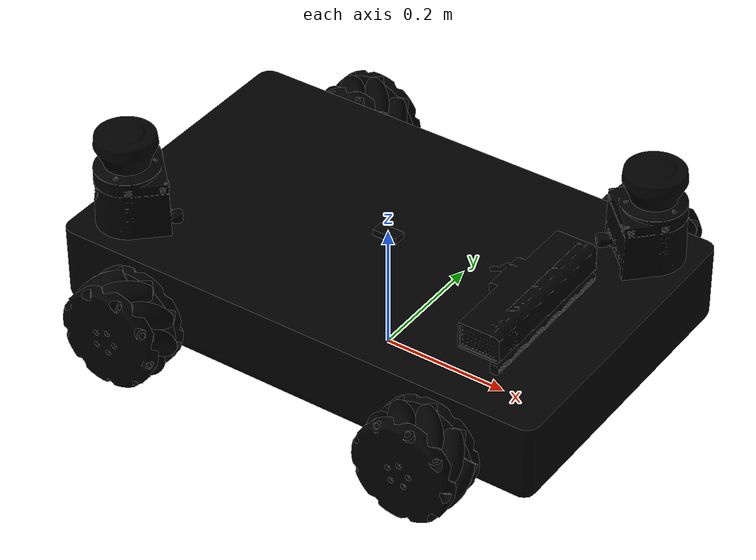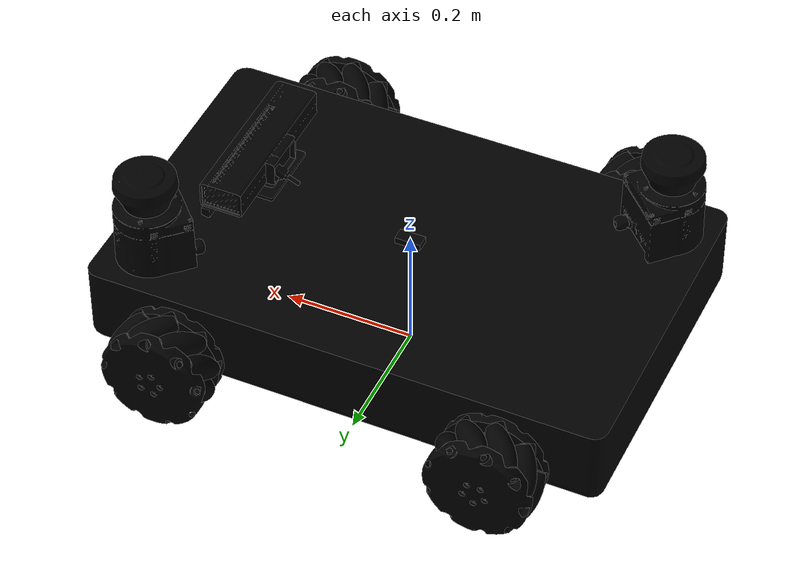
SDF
<?xml version='1.0' encoding='utf-8'?>
<sdf version="1.6">
  <world name="default">

    <gravity>0 0 0</gravity>
    <physics default="0" name="default_physics" type="ode">
      <max_step_size>0.005</max_step_size>
      <real_time_factor>1.0</real_time_factor>
      <real_time_update_rate>1000</real_time_update_rate>
    </physics>

    <plugin name='ignition::gazebo::systems::Physics' filename='libignition-gazebo-physics-system.so'/>
    <plugin name='ignition::gazebo::systems::UserCommands' filename='libignition-gazebo-user-commands-system.so'/>
    <plugin name='ignition::gazebo::systems::SceneBroadcaster' filename='libignition-gazebo-scene-broadcaster-system.so'/>
    <plugin name='ignition::gazebo::systems::Imu' filename='ignition-gazebo-imu-system'/>
    <plugin name='ignition::gazebo::systems::Sensors' filename='ignition-gazebo-sensors-system'>
        <render_engine>ogre2</render_engine>
    </plugin>

  <include>
      <uri>model://zm_robot</uri>
      <name>zm_robot</name>
      <pose>0 0 0.03 0 0 0</pose>
    </include>

    <gui fullscreen='0'>
      <camera name='user_camera'>
        <pose frame=''>-4.70385 10.895 16.2659 -0 0.921795 -1.12701</pose>
        <view_controller>orbit</view_controller>
        <projection_type>perspective</projection_type>
      </camera>
    </gui>

  </world>
</sdf>

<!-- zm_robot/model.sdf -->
<sdf version='1.6'>
  <model name='zm_robot'>
    <link name='base_link'>
      <self_collide>false</self_collide>
      <pose frame=''>0 0 0.081572 0 0 0</pose>
      <static>false</static>
	    <inertial>
          <mass>29.964</mass>
          <pose>0 0 0 0 0 0</pose>
          <inertia>
            <ixx>0.892684320</ixx>
            <ixy>0</ixy>
            <ixz>0</ixz>
            <iyy>1.966612482</iyy>
            <iyz>0</iyz>
            <izz>2.677227828</izz>
          </inertia>
      </inertial>
      <kinematic>0</kinematic>
      <gravity>1</gravity>
      <visual name='base_link_visual'>
        <geometry>
          <mesh>
            <uri>meshes/Base/agv_base.stl</uri>
            <scale>0.01 0.01 0.01</scale>  <!-- Scale mesh by 1.5 on all axes -->
          </mesh>
        </geometry>
        <material>
          <ambient>0.0 0.0 0 1</ambient>
          <diffuse>0.0 0.0 0 1</diffuse>
          <specular>0 0 0 1</specular>
          <emissive>1 0.423 0.0423 1.0</emissive>
        </material>
      </visual>
      <collision name='base_link_collosion'>
        <laser_retro>0</laser_retro>
        <max_contacts>10</max_contacts>
        <pose>0 0 0 0 0 0</pose>
        <geometry>
          <mesh>
            <uri>meshes/Base/agv_base.stl</uri>
            <scale>0.01 0.01 0.01</scale>
          </mesh>
        </geometry>
        <surface>
          <friction>
            <ode>
              <mu>0.4</mu>
              <mu2>0.4</mu2>
              <fdir1>0 0 0</fdir1>
              <slip1>0</slip1>
              <slip2>0</slip2>
              </ode>
            <torsional>
              <coefficient>1</coefficient>
              <patch_radius>0</patch_radius>
              <surface_radius>0</surface_radius>
              <use_patch_radius>1</use_patch_radius>
              <ode>
                <slip>0</slip>
              </ode>
            </torsional>
          </friction>
        </surface>
      </collision>
    </link>
    <link name="imu_link">
      <self_collide>false</self_collide>
      <pose frame='base_link'>0 0 0.08 0 0 0</pose>
      <static>false</static>
	    <inertial>
          <mass>0.5</mass>
          <pose>0 0 0 0 0 0</pose>
          <inertia>
            <ixx>0.00005</ixx>
            <ixy>0</ixy>
            <ixz>0</ixz>
            <iyy>0.00005</iyy>
            <iyz>0</iyz>
            <izz>0.00005</izz>
          </inertia>
      </inertial>
      <kinematic>0</kinematic>
      <gravity>1</gravity>
      <visual name='imu_link_visual'>
        <geometry>
          <mesh>
            <uri>meshes/Imu/IMU_sensor.stl</uri>
            <scale>0.01 0.01 0.01</scale>  <!-- Scale mesh by 1.5 on all axes -->
          </mesh>
        </geometry>
        <material>
          <ambient>0.0 0.0 0 1</ambient>
          <diffuse>0.0 0.0 0 1</diffuse>
          <specular>0 0 0 1</specular>
          <emissive>1 0 0 1.0</emissive>
        </material>
      </visual>
      <collision name='imu_link_collosion'>
        <laser_retro>0</laser_retro>
        <max_contacts>10</max_contacts>
        <pose>0 0 0 0 0 0</pose>
        <geometry>
          <mesh>
            <uri>meshes/Imu/IMU_sensor.stl</uri>
            <scale>0.01 0.01 0.01</scale>
          </mesh>
        </geometry>
        <surface>
          <friction>
            <ode>
              <mu>0.4</mu>
              <mu2>0.4</mu2>
              <fdir1>0 0 0</fdir1>
              <slip1>0</slip1>
              <slip2>0</slip2>
              </ode>
            <torsional>
              <coefficient>1</coefficient>
              <patch_radius>0</patch_radius>
              <surface_radius>0</surface_radius>
              <use_patch_radius>1</use_patch_radius>
              <ode>
                <slip>0</slip>
              </ode>
            </torsional>
          </friction>
        </surface>
      </collision>
      <sensor name="imu" type="imu">
        <topic>/imu</topic>
        <update_rate>30</update_rate>
        <visualize>false</visualize>
      </sensor>
    </link>
    <joint name="imu_link_joint" type="fixed">
      <child>imu_link</child>
      <parent>base_link</parent>
    </joint>
    <link name="wheel_1_link">
      <self_collide>false</self_collide>
      <pose frame='base_link'>-0.25 0.3 0 -1.5708 0 0</pose>
      <static>false</static>
	    <inertial>
          <mass>1.7</mass>
          <pose>0 0 0 0 0 0</pose>
          <inertia>
            <ixx>0.04248052</ixx>
            <ixy>0</ixy>
            <ixz>0</ixz>
            <iyy>0.04248045</iyy>
            <iyz>0</iyz>
            <izz>0.04879970</izz>
          </inertia>
      </inertial>
      <kinematic>0</kinematic>
      <gravity>1</gravity>
      <visual name='wheel_1_visual'>
        <geometry>
          <mesh>
            <uri>meshes/WheelRL/mecanum_left_after.stl</uri>
            <scale>0.01 0.01 0.01</scale>  <!-- Scale mesh by 1.5 on all axes -->
          </mesh>
        </geometry>
        <material>
          <ambient>0.0 0.0 0 1</ambient>
          <diffuse>0.0 0.0 0 1</diffuse>
          <specular>0 0 0 1</specular>
          <emissive>0.2 0.2 0.2 1.0</emissive>
        </material>
      </visual>
      <collision name='wheel_1_collosion'>
        <laser_retro>0</laser_retro>
        <max_contacts>10</max_contacts>
        <pose>0 0 0 0 0 0</pose>
        <geometry>
          <mesh>
            <uri>meshes/WheelRL/mecanum_left_after.stl</uri>
            <scale>0.01 0.01 0.01</scale>
          </mesh>
        </geometry>
        <surface>
          <friction>
            <ode>
              <mu>0.4</mu>
              <mu2>0.4</mu2>
              <fdir1>0 0 0</fdir1>
              <slip1>0</slip1>
              <slip2>0</slip2>
              </ode>
            <torsional>
              <coefficient>1</coefficient>
              <patch_radius>0</patch_radius>
              <surface_radius>0</surface_radius>
              <use_patch_radius>1</use_patch_radius>
              <ode>
                <slip>0</slip>
              </ode>
            </torsional>
          </friction>
        </surface>
      </collision>
    </link>
    <joint name="wheel_1_joint" type="revolute">
      <child>wheel_1_link</child>
      <parent>base_link</parent>
    </joint>
    <link name="roller_1_1_link">
      <self_collide>false</self_collide>
      <pose frame='wheel_1_link'>0 0.065 0 0.7854 0 1.5708</pose>
      <static>false</static>
	    <inertial>
          <mass>0.124</mass>
          <pose>0 0 0 0 0 0</pose>
          <inertia>
            <ixx>0.0051893</ixx>
            <ixy>0</ixy>
            <ixz>0</ixz>
            <iyy>0.0051893</iyy>
            <iyz>0</iyz>
            <izz>0.0013891</izz>
          </inertia>
      </inertial>
      <kinematic>0</kinematic>
      <gravity>1</gravity>
      <visual name='roller_1_1_visual'>
        <geometry>
          <mesh>
            <uri>meshes/Roller/mecanum_roller.stl</uri>
            <scale>0.01 0.01 0.01</scale>  <!-- Scale mesh by 1.5 on all axes -->
          </mesh>
        </geometry>
        <material>
          <ambient>0.0 0.0 0 1</ambient>
          <diffuse>0.0 0.0 0 1</diffuse>
          <specular>0 0 0 1</specular>
          <emissive>0 0 0 1.0</emissive>
        </material>
      </visual>
      <collision name='roller_1_1_collosion'>
        <laser_retro>0</laser_retro>
        <max_contacts>10</max_contacts>
        <pose>0 0 0 0 0 0</pose>
        <geometry>
          <mesh>
            <uri>meshes/Roller/mecanum_roller.stl</uri>
            <scale>0.01 0.01 0.01</scale>
          </mesh>
        </geometry>
        <surface>
          <friction>
            <ode>
              <mu>0.4</mu>
              <mu2>0.4</mu2>
              <fdir1>0 0 0</fdir1>
              <slip1>0</slip1>
              <slip2>0</slip2>
              </ode>
            <torsional>
              <coefficient>1</coefficient>
              <patch_radius>0</patch_radius>
              <surface_radius>0</surface_radius>
              <use_patch_radius>1</use_patch_radius>
              <ode>
                <slip>0</slip>
              </ode>
            </torsional>
          </friction>
        </surface>
      </collision>
    </link>
    <joint name="roller_1_1_joint" type="revolute">
      <child>roller_1_1_link</child>
      <parent>wheel_1_link</parent>
    </joint>
    <link name="roller_1_2_link">
      <self_collide>false</self_collide>
      <pose frame='wheel_1_link'>0.041781 0.049792 0 0.7854 0 0.8727</pose>
      <static>false</static>
	    <inertial>
          <mass>0.124</mass>
          <pose>0 0 0 0 0 0</pose>
          <inertia>
            <ixx>0.0051893</ixx>
            <ixy>0</ixy>
            <ixz>0</ixz>
            <iyy>0.0051893</iyy>
            <iyz>0</iyz>
            <izz>0.0013891</izz>
          </inertia>
      </inertial>
      <kinematic>0</kinematic>
      <gravity>1</gravity>
      <visual name='roller_1_2__visual'>
        <geometry>
          <mesh>
            <uri>meshes/Roller/mecanum_roller.stl</uri>
            <scale>0.01 0.01 0.01</scale>  <!-- Scale mesh by 1.5 on all axes -->
          </mesh>
        </geometry>
        <material>
          <ambient>0.0 0.0 0 1</ambient>
          <diffuse>0.0 0.0 0 1</diffuse>
          <specular>0 0 0 1</specular>
          <emissive>0 0 0 1.0</emissive>
        </material>
      </visual>
      <collision name='roller_1_2_collosion'>
        <laser_retro>0</laser_retro>
        <max_contacts>10</max_contacts>
        <pose>0 0 0 0 0 0</pose>
        <geometry>
          <mesh>
            <uri>meshes/Roller/mecanum_roller.stl</uri>
            <scale>0.01 0.01 0.01</scale>
          </mesh>
        </geometry>
        <surface>
          <friction>
            <ode>
              <mu>0.4</mu>
              <mu2>0.4</mu2>
              <fdir1>0 0 0</fdir1>
              <slip1>0</slip1>
              <slip2>0</slip2>
              </ode>
            <torsional>
              <coefficient>1</coefficient>
              <patch_radius>0</patch_radius>
              <surface_radius>0</surface_radius>
              <use_patch_radius>1</use_patch_radius>
              <ode>
                <slip>0</slip>
              </ode>
            </torsional>
          </friction>
        </surface>
      </collision>
    </link>
    <joint name="roller_1_2_joint" type="revolute">
      <child>roller_1_2_link</child>
      <parent>wheel_1_link</parent>
    </joint>
    <link name="roller_1_3_link">
      <self_collide>false</self_collide>
      <pose frame='wheel_1_link'>0.064012 0.011287 0 0.7854 0 0.1746</pose>
      <static>false</static>
	    <inertial>
          <mass>0.124</mass>
          <pose>0 0 0 0 0 0</pose>
          <inertia>
            <ixx>0.0051893</ixx>
            <ixy>0</ixy>
            <ixz>0</ixz>
            <iyy>0.0051893</iyy>
            <iyz>0</iyz>
            <izz>0.0013891</izz>
          </inertia>
      </inertial>
      <kinematic>0</kinematic>
      <gravity>1</gravity>
      <visual name='roller_1_3_visual'>
        <geometry>
          <mesh>
            <uri>meshes/Roller/mecanum_roller.stl</uri>
            <scale>0.01 0.01 0.01</scale>  <!-- Scale mesh by 1.5 on all axes -->
          </mesh>
        </geometry>
        <material>
          <ambient>0.0 0.0 0 1</ambient>
          <diffuse>0.0 0.0 0 1</diffuse>
          <specular>0 0 0 1</specular>
          <emissive>0 0 0 1.0</emissive>
        </material>
      </visual>
      <collision name='roller_1_3_collosion'>
        <laser_retro>0</laser_retro>
        <max_contacts>10</max_contacts>
        <pose>0 0 0 0 0 0</pose>
        <geometry>
          <mesh>
            <uri>meshes/Roller/mecanum_roller.stl</uri>
            <scale>0.01 0.01 0.01</scale>
          </mesh>
        </geometry>
        <surface>
          <friction>
            <ode>
              <mu>0.4</mu>
              <mu2>0.4</mu2>
              <fdir1>0 0 0</fdir1>
              <slip1>0</slip1>
              <slip2>0</slip2>
              </ode>
            <torsional>
              <coefficient>1</coefficient>
              <patch_radius>0</patch_radius>
              <surface_radius>0</surface_radius>
              <use_patch_radius>1</use_patch_radius>
              <ode>
                <slip>0</slip>
              </ode>
            </torsional>
          </friction>
        </surface>
      </collision>
    </link>
    <joint name="roller_1_3_joint" type="revolute">
      <child>roller_1_3_link</child>
      <parent>wheel_1_link</parent>
    </joint>
    <link name="roller_1_4_link">
      <self_collide>false</self_collide>
      <pose frame='wheel_1_link'>0.056291 -0.0325 0 0.7854 0 -0.5235</pose>
      <static>false</static>
	    <inertial>
          <mass>0.124</mass>
          <pose>0 0 0 0 0 0</pose>
          <inertia>
            <ixx>0.0051893</ixx>
            <ixy>0</ixy>
            <ixz>0</ixz>
            <iyy>0.0051893</iyy>
            <iyz>0</iyz>
            <izz>0.0013891</izz>
          </inertia>
      </inertial>
      <kinematic>0</kinematic>
      <gravity>1</gravity>
      <visual name='roller_1_4_visual'>
        <geometry>
          <mesh>
            <uri>meshes/Roller/mecanum_roller.stl</uri>
            <scale>0.01 0.01 0.01</scale>  <!-- Scale mesh by 1.5 on all axes -->
          </mesh>
        </geometry>
        <material>
          <ambient>0.0 0.0 0 1</ambient>
          <diffuse>0.0 0.0 0 1</diffuse>
          <specular>0 0 0 1</specular>
          <emissive>0 0 0 1.0</emissive>
        </material>
      </visual>
      <collision name='roller_1_4_collosion'>
        <laser_retro>0</laser_retro>
        <max_contacts>10</max_contacts>
        <pose>0 0 0 0 0 0</pose>
        <geometry>
          <mesh>
            <uri>meshes/Roller/mecanum_roller.stl</uri>
            <scale>0.01 0.01 0.01</scale>
          </mesh>
        </geometry>
        <surface>
          <friction>
            <ode>
              <mu>0.4</mu>
              <mu2>0.4</mu2>
              <fdir1>0 0 0</fdir1>
              <slip1>0</slip1>
              <slip2>0</slip2>
              </ode>
            <torsional>
              <coefficient>1</coefficient>
              <patch_radius>0</patch_radius>
              <surface_radius>0</surface_radius>
              <use_patch_radius>1</use_patch_radius>
              <ode>
                <slip>0</slip>
              </ode>
            </torsional>
          </friction>
        </surface>
      </collision>
    </link>
    <joint name="roller_1_4_joint" type="revolute">
      <child>roller_1_4_link</child>
      <parent>wheel_1_link</parent>
    </joint>
    <link name="roller_1_5_link">
      <self_collide>false</self_collide>
      <pose frame='wheel_1_link'>0.022231 -0.06108 0 0.7854 0 -1.2216</pose>
      <static>false</static>
	    <inertial>
          <mass>0.124</mass>
          <pose>0 0 0 0 0 0</pose>
          <inertia>
            <ixx>0.0051893</ixx>
            <ixy>0</ixy>
            <ixz>0</ixz>
            <iyy>0.0051893</iyy>
            <iyz>0</iyz>
            <izz>0.0013891</izz>
          </inertia>
      </inertial>
      <kinematic>0</kinematic>
      <gravity>1</gravity>
      <visual name='roller_1_5_visual'>
        <geometry>
          <mesh>
            <uri>meshes/Roller/mecanum_roller.stl</uri>
            <scale>0.01 0.01 0.01</scale>  <!-- Scale mesh by 1.5 on all axes -->
          </mesh>
        </geometry>
        <material>
          <ambient>0.0 0.0 0 1</ambient>
          <diffuse>0.0 0.0 0 1</diffuse>
          <specular>0 0 0 1</specular>
          <emissive>0 0 0 1.0</emissive>
        </material>
      </visual>
      <collision name='roller_1_5_collosion'>
        <laser_retro>0</laser_retro>
        <max_contacts>10</max_contacts>
        <pose>0 0 0 0 0 0</pose>
        <geometry>
          <mesh>
            <uri>meshes/Roller/mecanum_roller.stl</uri>
            <scale>0.01 0.01 0.01</scale>
          </mesh>
        </geometry>
        <surface>
          <friction>
            <ode>
              <mu>0.4</mu>
              <mu2>0.4</mu2>
              <fdir1>0 0 0</fdir1>
              <slip1>0</slip1>
              <slip2>0</slip2>
              </ode>
            <torsional>
              <coefficient>1</coefficient>
              <patch_radius>0</patch_radius>
              <surface_radius>0</surface_radius>
              <use_patch_radius>1</use_patch_radius>
              <ode>
                <slip>0</slip>
              </ode>
            </torsional>
          </friction>
        </surface>
      </collision>
    </link>
    <joint name="roller_1_5_joint" type="revolute">
      <child>roller_1_5_link</child>
      <parent>wheel_1_link</parent>
    </joint>
    <link name="roller_1_6_link">
      <self_collide>false</self_collide>
      <pose frame='wheel_1_link'>-0.022231 -0.06108 0 0.7854 0 4.3632</pose>
      <static>false</static>
	    <inertial>
          <mass>0.124</mass>
          <pose>0 0 0 0 0 0</pose>
          <inertia>
            <ixx>0.0051893</ixx>
            <ixy>0</ixy>
            <ixz>0</ixz>
            <iyy>0.0051893</iyy>
            <iyz>0</iyz>
            <izz>0.0013891</izz>
          </inertia>
      </inertial>
      <kinematic>0</kinematic>
      <gravity>1</gravity>
      <visual name='roller_1_6_visual'>
        <geometry>
          <mesh>
            <uri>meshes/Roller/mecanum_roller.stl</uri>
            <scale>0.01 0.01 0.01</scale>  <!-- Scale mesh by 1.5 on all axes -->
          </mesh>
        </geometry>
        <material>
          <ambient>0.0 0.0 0 1</ambient>
          <diffuse>0.0 0.0 0 1</diffuse>
          <specular>0 0 0 1</specular>
          <emissive>0 0 0 1.0</emissive>
        </material>
      </visual>
      <collision name='roller_1_6_collosion'>
        <laser_retro>0</laser_retro>
        <max_contacts>10</max_contacts>
        <pose>0 0 0 0 0 0</pose>
        <geometry>
          <mesh>
            <uri>meshes/Roller/mecanum_roller.stl</uri>
            <scale>0.01 0.01 0.01</scale>
          </mesh>
        </geometry>
        <surface>
          <friction>
            <ode>
              <mu>0.4</mu>
              <mu2>0.4</mu2>
              <fdir1>0 0 0</fdir1>
              <slip1>0</slip1>
              <slip2>0</slip2>
              </ode>
            <torsional>
              <coefficient>1</coefficient>
              <patch_radius>0</patch_radius>
              <surface_radius>0</surface_radius>
              <use_patch_radius>1</use_patch_radius>
              <ode>
                <slip>0</slip>
              </ode>
            </torsional>
          </friction>
        </surface>
      </collision>
    </link>
    <joint name="roller_1_6_joint" type="revolute">
      <child>roller_1_6_link</child>
      <parent>wheel_1_link</parent>
    </joint>
    <link name="roller_1_7_link">
      <self_collide>false</self_collide>
      <pose frame='wheel_1_link'>-0.056291 -0.0325 0 0.7854 0 3.6651</pose>
      <static>false</static>
	    <inertial>
          <mass>0.124</mass>
          <pose>0 0 0 0 0 0</pose>
          <inertia>
            <ixx>0.0051893</ixx>
            <ixy>0</ixy>
            <ixz>0</ixz>
            <iyy>0.0051893</iyy>
            <iyz>0</iyz>
            <izz>0.0013891</izz>
          </inertia>
      </inertial>
      <kinematic>0</kinematic>
      <gravity>1</gravity>
      <visual name='roller_1_7_visual'>
        <geometry>
          <mesh>
            <uri>meshes/Roller/mecanum_roller.stl</uri>
            <scale>0.01 0.01 0.01</scale>  <!-- Scale mesh by 1.5 on all axes -->
          </mesh>
        </geometry>
        <material>
          <ambient>0.0 0.0 0 1</ambient>
          <diffuse>0.0 0.0 0 1</diffuse>
          <specular>0 0 0 1</specular>
          <emissive>0 0 0 1.0</emissive>
        </material>
      </visual>
      <collision name='roller_1_7_collosion'>
        <laser_retro>0</laser_retro>
        <max_contacts>10</max_contacts>
        <pose>0 0 0 0 0 0</pose>
        <geometry>
          <mesh>
            <uri>meshes/Roller/mecanum_roller.stl</uri>
            <scale>0.01 0.01 0.01</scale>
          </mesh>
        </geometry>
        <surface>
          <friction>
            <ode>
              <mu>0.4</mu>
              <mu2>0.4</mu2>
              <fdir1>0 0 0</fdir1>
              <slip1>0</slip1>
              <slip2>0</slip2>
              </ode>
            <torsional>
              <coefficient>1</coefficient>
              <patch_radius>0</patch_radius>
              <surface_radius>0</surface_radius>
              <use_patch_radius>1</use_patch_radius>
              <ode>
                <slip>0</slip>
              </ode>
            </torsional>
          </friction>
        </surface>
      </collision>
    </link>
    <joint name="roller_1_7_joint" type="revolute">
      <child>roller_1_7_link</child>
      <parent>wheel_1_link</parent>
    </joint>
    <link name="roller_1_8_link">
      <self_collide>false</self_collide>
      <pose frame='wheel_1_link'>-0.064012 0.011287 0 0.7854 0 2.967</pose>
      <static>false</static>
	    <inertial>
          <mass>0.124</mass>
          <pose>0 0 0 0 0 0</pose>
          <inertia>
            <ixx>0.0051893</ixx>
            <ixy>0</ixy>
            <ixz>0</ixz>
            <iyy>0.0051893</iyy>
            <iyz>0</iyz>
            <izz>0.0013891</izz>
          </inertia>
      </inertial>
      <kinematic>0</kinematic>
      <gravity>1</gravity>
      <visual name='roller_1_8_visual'>
        <geometry>
          <mesh>
            <uri>meshes/Roller/mecanum_roller.stl</uri>
            <scale>0.01 0.01 0.01</scale>  <!-- Scale mesh by 1.5 on all axes -->
          </mesh>
        </geometry>
        <material>
          <ambient>0.0 0.0 0 1</ambient>
          <diffuse>0.0 0.0 0 1</diffuse>
          <specular>0 0 0 1</specular>
          <emissive>0 0 0 1.0</emissive>
        </material>
      </visual>
      <collision name='roller_1_8_collosion'>
        <laser_retro>0</laser_retro>
        <max_contacts>10</max_contacts>
        <pose>0 0 0 0 0 0</pose>
        <geometry>
          <mesh>
            <uri>meshes/Roller/mecanum_roller.stl</uri>
            <scale>0.01 0.01 0.01</scale>
          </mesh>
        </geometry>
        <surface>
          <friction>
            <ode>
              <mu>0.4</mu>
              <mu2>0.4</mu2>
              <fdir1>0 0 0</fdir1>
              <slip1>0</slip1>
              <slip2>0</slip2>
              </ode>
            <torsional>
              <coefficient>1</coefficient>
              <patch_radius>0</patch_radius>
              <surface_radius>0</surface_radius>
              <use_patch_radius>1</use_patch_radius>
              <ode>
                <slip>0</slip>
              </ode>
            </torsional>
          </friction>
        </surface>
      </collision>
    </link>
    <joint name="roller_1_8_joint" type="revolute">
      <child>roller_1_8_link</child>
      <parent>wheel_1_link</parent>
    </joint>
    <link name="roller_1_9_link">
      <self_collide>false</self_collide>
      <pose frame='wheel_1_link'>-0.041781 0.049792 0 0.7854 0 2.2689</pose>
      <static>false</static>
	    <inertial>
          <mass>0.124</mass>
          <pose>0 0 0 0 0 0</pose>
          <inertia>
            <ixx>0.0051893</ixx>
            <ixy>0</ixy>
            <ixz>0</ixz>
            <iyy>0.0051893</iyy>
            <iyz>0</iyz>
            <izz>0.0013891</izz>
          </inertia>
      </inertial>
      <kinematic>0</kinematic>
      <gravity>1</gravity>
      <visual name='roller_1_9_visual'>
        <geometry>
          <mesh>
            <uri>meshes/Roller/mecanum_roller.stl</uri>
            <scale>0.01 0.01 0.01</scale>  <!-- Scale mesh by 1.5 on all axes -->
          </mesh>
        </geometry>
        <material>
          <ambient>0.0 0.0 0 1</ambient>
          <diffuse>0.0 0.0 0 1</diffuse>
          <specular>0 0 0 1</specular>
          <emissive>0 0 0 1.0</emissive>
        </material>
      </visual>
      <collision name='roller_1_9_collosion'>
        <laser_retro>0</laser_retro>
        <max_contacts>10</max_contacts>
        <pose>0 0 0 0 0 0</pose>
        <geometry>
          <mesh>
            <uri>meshes/Roller/mecanum_roller.stl</uri>
            <scale>0.01 0.01 0.01</scale>
          </mesh>
        </geometry>
        <surface>
          <friction>
            <ode>
              <mu>0.4</mu>
              <mu2>0.4</mu2>
              <fdir1>0 0 0</fdir1>
              <slip1>0</slip1>
              <slip2>0</slip2>
              </ode>
            <torsional>
              <coefficient>1</coefficient>
              <patch_radius>0</patch_radius>
              <surface_radius>0</surface_radius>
              <use_patch_radius>1</use_patch_radius>
              <ode>
                <slip>0</slip>
              </ode>
            </torsional>
          </friction>
        </surface>
      </collision>
    </link>
    <joint name="roller_1_9_joint" type="revolute">
      <child>roller_1_9_link</child>
      <parent>wheel_1_link</parent>
    </joint>
    <link name="wheel_2_link">
      <self_collide>false</self_collide>
      <pose frame='base_link'>0.25 0.3 0 -1.5708 0 0</pose>
      <static>false</static>
	    <inertial>
          <mass>1.7</mass>
          <pose>0 0 0 0 0 0</pose>
          <inertia>
            <ixx>0.04248052</ixx>
            <ixy>0</ixy>
            <ixz>0</ixz>
            <iyy>0.04248045</iyy>
            <iyz>0</iyz>
            <izz>0.04879970</izz>
          </inertia>
      </inertial>
      <kinematic>0</kinematic>
      <gravity>1</gravity>
      <visual name='wheel_2_visual'>
        <geometry>
          <mesh>
            <uri>meshes/WheelFL/mecanum_left_before.stl</uri>
            <scale>0.01 0.01 0.01</scale>  <!-- Scale mesh by 1.5 on all axes -->
          </mesh>
        </geometry>
        <material>
          <ambient>0.0 0.0 0 1</ambient>
          <diffuse>0.0 0.0 0 1</diffuse>
          <specular>0 0 0 1</specular>
          <emissive>0.2 0.2 0.2 1.0</emissive>
        </material>
      </visual>
      <collision name='wheel_2_collosion'>
        <laser_retro>0</laser_retro>
        <max_contacts>10</max_contacts>
        <pose>0 0 0 0 0 0</pose>
        <geometry>
          <mesh>
            <uri>meshes/WheelFL/mecanum_left_before.stl</uri>
            <scale>0.01 0.01 0.01</scale>
          </mesh>
        </geometry>
        <surface>
          <friction>
            <ode>
              <mu>0.4</mu>
              <mu2>0.4</mu2>
              <fdir1>0 0 0</fdir1>
              <slip1>0</slip1>
              <slip2>0</slip2>
              </ode>
            <torsional>
              <coefficient>1</coefficient>
              <patch_radius>0</patch_radius>
              <surface_radius>0</surface_radius>
              <use_patch_radius>1</use_patch_radius>
              <ode>
                <slip>0</slip>
              </ode>
            </torsional>
          </friction>
        </surface>
      </collision>
    </link>
    <joint name="wheel_2_joint" type="revolute">
      <child>wheel_2_link</child>
      <parent>base_link</parent>
    </joint>
    <link name="roller_2_1_link">
      <self_collide>false</self_collide>
      <pose frame='wheel_2_link'>0.065 0 0 -0.7854 0 0</pose>
      <static>false</static>
	    <inertial>
          <mass>0.124</mass>
          <pose>0 0 0 0 0 0</pose>
          <inertia>
            <ixx>0.0051893</ixx>
            <ixy>0</ixy>
            <ixz>0</ixz>
            <iyy>0.0051893</iyy>
            <iyz>0</iyz>
            <izz>0.0013891</izz>
          </inertia>
      </inertial>
      <kinematic>0</kinematic>
      <gravity>1</gravity>
      <visual name='roller_2_1_visual'>
        <geometry>
          <mesh>
            <uri>meshes/Roller/mecanum_roller.stl</uri>
            <scale>0.01 0.01 0.01</scale>  <!-- Scale mesh by 1.5 on all axes -->
          </mesh>
        </geometry>
        <material>
          <ambient>0.0 0.0 0 1</ambient>
          <diffuse>0.0 0.0 0 1</diffuse>
          <specular>0 0 0 1</specular>
          <emissive>0 0 0 1.0</emissive>
        </material>
      </visual>
      <collision name='roller_2_1_collosion'>
        <laser_retro>0</laser_retro>
        <max_contacts>10</max_contacts>
        <pose>0 0 0 0 0 0</pose>
        <geometry>
          <mesh>
            <uri>meshes/Roller/mecanum_roller.stl</uri>
            <scale>0.01 0.01 0.01</scale>
          </mesh>
        </geometry>
        <surface>
          <friction>
            <ode>
              <mu>0.4</mu>
              <mu2>0.4</mu2>
              <fdir1>0 0 0</fdir1>
              <slip1>0</slip1>
              <slip2>0</slip2>
              </ode>
            <torsional>
              <coefficient>1</coefficient>
              <patch_radius>0</patch_radius>
              <surface_radius>0</surface_radius>
              <use_patch_radius>1</use_patch_radius>
              <ode>
                <slip>0</slip>
              </ode>
            </torsional>
          </friction>
        </surface>
      </collision>
    </link>
    <joint name="roller_2_1_joint" type="revolute">
      <child>roller_2_1_link</child>
      <parent>wheel_2_link</parent>
    </joint>
    <link name="roller_2_2_link">
      <self_collide>false</self_collide>
      <pose frame='wheel_2_link'>0.049792 0.041781 0 -0.7854 0 0.6981</pose>
      <static>false</static>
	    <inertial>
          <mass>0.124</mass>
          <pose>0 0 0 0 0 0</pose>
          <inertia>
            <ixx>0.0051893</ixx>
            <ixy>0</ixy>
            <ixz>0</ixz>
            <iyy>0.0051893</iyy>
            <iyz>0</iyz>
            <izz>0.0013891</izz>
          </inertia>
      </inertial>
      <kinematic>0</kinematic>
      <gravity>1</gravity>
      <visual name='roller_2_2__visual'>
        <geometry>
          <mesh>
            <uri>meshes/Roller/mecanum_roller.stl</uri>
            <scale>0.01 0.01 0.01</scale>  <!-- Scale mesh by 1.5 on all axes -->
          </mesh>
        </geometry>
        <material>
          <ambient>0.0 0.0 0 1</ambient>
          <diffuse>0.0 0.0 0 1</diffuse>
          <specular>0 0 0 1</specular>
          <emissive>0 0 0 1.0</emissive>
        </material>
      </visual>
      <collision name='roller_2_2_collosion'>
        <laser_retro>0</laser_retro>
        <max_contacts>10</max_contacts>
        <pose>0 0 0 0 0 0</pose>
        <geometry>
          <mesh>
            <uri>meshes/Roller/mecanum_roller.stl</uri>
            <scale>0.01 0.01 0.01</scale>
          </mesh>
        </geometry>
        <surface>
          <friction>
            <ode>
              <mu>0.4</mu>
              <mu2>0.4</mu2>
              <fdir1>0 0 0</fdir1>
              <slip1>0</slip1>
              <slip2>0</slip2>
              </ode>
            <torsional>
              <coefficient>1</coefficient>
              <patch_radius>0</patch_radius>
              <surface_radius>0</surface_radius>
              <use_patch_radius>1</use_patch_radius>
              <ode>
                <slip>0</slip>
              </ode>
            </torsional>
          </friction>
        </surface>
      </collision>
    </link>
    <joint name="roller_2_2_joint" type="revolute">
      <child>roller_2_2_link</child>
      <parent>wheel_2_link</parent>
    </joint>
    <link name="roller_2_3_link">
      <self_collide>false</self_collide>
      <pose frame='wheel_2_link'>0.011287 0.064012 0 -0.7854 0 1.3962</pose>
      <static>false</static>
	    <inertial>
          <mass>0.124</mass>
          <pose>0 0 0 0 0 0</pose>
          <inertia>
            <ixx>0.0051893</ixx>
            <ixy>0</ixy>
            <ixz>0</ixz>
            <iyy>0.0051893</iyy>
            <iyz>0</iyz>
            <izz>0.0013891</izz>
          </inertia>
      </inertial>
      <kinematic>0</kinematic>
      <gravity>1</gravity>
      <visual name='roller_2_3_visual'>
        <geometry>
          <mesh>
            <uri>meshes/Roller/mecanum_roller.stl</uri>
            <scale>0.01 0.01 0.01</scale>  <!-- Scale mesh by 1.5 on all axes -->
          </mesh>
        </geometry>
        <material>
          <ambient>0.0 0.0 0 1</ambient>
          <diffuse>0.0 0.0 0 1</diffuse>
          <specular>0 0 0 1</specular>
          <emissive>0 0 0 1.0</emissive>
        </material>
      </visual>
      <collision name='roller_2_3_collosion'>
        <laser_retro>0</laser_retro>
        <max_contacts>10</max_contacts>
        <pose>0 0 0 0 0 0</pose>
        <geometry>
          <mesh>
            <uri>meshes/Roller/mecanum_roller.stl</uri>
            <scale>0.01 0.01 0.01</scale>
          </mesh>
        </geometry>
        <surface>
          <friction>
            <ode>
              <mu>0.4</mu>
              <mu2>0.4</mu2>
              <fdir1>0 0 0</fdir1>
              <slip1>0</slip1>
              <slip2>0</slip2>
              </ode>
            <torsional>
              <coefficient>1</coefficient>
              <patch_radius>0</patch_radius>
              <surface_radius>0</surface_radius>
              <use_patch_radius>1</use_patch_radius>
              <ode>
                <slip>0</slip>
              </ode>
            </torsional>
          </friction>
        </surface>
      </collision>
    </link>
    <joint name="roller_2_3_joint" type="revolute">
      <child>roller_2_3_link</child>
      <parent>wheel_2_link</parent>
    </joint>
    <link name="roller_2_4_link">
      <self_collide>false</self_collide>
      <pose frame='wheel_2_link'>-0.0325 0.056291 0 0.7854 0 2.0943</pose>
      <static>false</static>
	    <inertial>
          <mass>0.124</mass>
          <pose>0 0 0 0 0 0</pose>
          <inertia>
            <ixx>0.0051893</ixx>
            <ixy>0</ixy>
            <ixz>0</ixz>
            <iyy>0.0051893</iyy>
            <iyz>0</iyz>
            <izz>0.0013891</izz>
          </inertia>
      </inertial>
      <kinematic>0</kinematic>
      <gravity>1</gravity>
      <visual name='roller_2_4_visual'>
        <geometry>
          <mesh>
            <uri>meshes/Roller/mecanum_roller.stl</uri>
            <scale>0.01 0.01 0.01</scale>  <!-- Scale mesh by 1.5 on all axes -->
          </mesh>
        </geometry>
        <material>
          <ambient>0.0 0.0 0 1</ambient>
          <diffuse>0.0 0.0 0 1</diffuse>
          <specular>0 0 0 1</specular>
          <emissive>0 0 0 1.0</emissive>
        </material>
      </visual>
      <collision name='roller_2_4_collosion'>
        <laser_retro>0</laser_retro>
        <max_contacts>10</max_contacts>
        <pose>0 0 0 0 0 0</pose>
        <geometry>
          <mesh>
            <uri>meshes/Roller/mecanum_roller.stl</uri>
            <scale>0.01 0.01 0.01</scale>
          </mesh>
        </geometry>
        <surface>
          <friction>
            <ode>
              <mu>0.4</mu>
              <mu2>0.4</mu2>
              <fdir1>0 0 0</fdir1>
              <slip1>0</slip1>
              <slip2>0</slip2>
              </ode>
            <torsional>
              <coefficient>1</coefficient>
              <patch_radius>0</patch_radius>
              <surface_radius>0</surface_radius>
              <use_patch_radius>1</use_patch_radius>
              <ode>
                <slip>0</slip>
              </ode>
            </torsional>
          </friction>
        </surface>
      </collision>
    </link>
    <joint name="roller_2_4_joint" type="revolute">
      <child>roller_2_4_link</child>
      <parent>wheel_2_link</parent>
    </joint>
    <link name="roller_2_5_link">
      <self_collide>false</self_collide>
      <pose frame='wheel_2_link'>-0.06108 0.022231 0 -0.7854 0 2.7924</pose>
      <static>false</static>
	    <inertial>
          <mass>0.124</mass>
          <pose>0 0 0 0 0 0</pose>
          <inertia>
            <ixx>0.0051893</ixx>
            <ixy>0</ixy>
            <ixz>0</ixz>
            <iyy>0.0051893</iyy>
            <iyz>0</iyz>
            <izz>0.0013891</izz>
          </inertia>
      </inertial>
      <kinematic>0</kinematic>
      <gravity>1</gravity>
      <visual name='roller_2_5_visual'>
        <geometry>
          <mesh>
            <uri>meshes/Roller/mecanum_roller.stl</uri>
            <scale>0.01 0.01 0.01</scale>  <!-- Scale mesh by 1.5 on all axes -->
          </mesh>
        </geometry>
        <material>
          <ambient>0.0 0.0 0 1</ambient>
          <diffuse>0.0 0.0 0 1</diffuse>
          <specular>0 0 0 1</specular>
          <emissive>0 0 0 1.0</emissive>
        </material>
      </visual>
      <collision name='roller_2_5_collosion'>
        <laser_retro>0</laser_retro>
        <max_contacts>10</max_contacts>
        <pose>0 0 0 0 0 0</pose>
        <geometry>
          <mesh>
            <uri>meshes/Roller/mecanum_roller.stl</uri>
            <scale>0.01 0.01 0.01</scale>
          </mesh>
        </geometry>
        <surface>
          <friction>
            <ode>
              <mu>0.4</mu>
              <mu2>0.4</mu2>
              <fdir1>0 0 0</fdir1>
              <slip1>0</slip1>
              <slip2>0</slip2>
              </ode>
            <torsional>
              <coefficient>1</coefficient>
              <patch_radius>0</patch_radius>
              <surface_radius>0</surface_radius>
              <use_patch_radius>1</use_patch_radius>
              <ode>
                <slip>0</slip>
              </ode>
            </torsional>
          </friction>
        </surface>
      </collision>
    </link>
    <joint name="roller_2_5_joint" type="revolute">
      <child>roller_2_5_link</child>
      <parent>wheel_2_link</parent>
    </joint>
    <link name="roller_2_6_link">
      <self_collide>false</self_collide>
      <pose frame='wheel_2_link'>-0.06108 -0.022231 0 -0.7854 0 -2.794</pose>
      <static>false</static>
	    <inertial>
          <mass>0.124</mass>
          <pose>0 0 0 0 0 0</pose>
          <inertia>
            <ixx>0.0051893</ixx>
            <ixy>0</ixy>
            <ixz>0</ixz>
            <iyy>0.0051893</iyy>
            <iyz>0</iyz>
            <izz>0.0013891</izz>
          </inertia>
      </inertial>
      <kinematic>0</kinematic>
      <gravity>1</gravity>
      <visual name='roller_2_6_visual'>
        <geometry>
          <mesh>
            <uri>meshes/Roller/mecanum_roller.stl</uri>
            <scale>0.01 0.01 0.01</scale>  <!-- Scale mesh by 1.5 on all axes -->
          </mesh>
        </geometry>
        <material>
          <ambient>0.0 0.0 0 1</ambient>
          <diffuse>0.0 0.0 0 1</diffuse>
          <specular>0 0 0 1</specular>
          <emissive>0 0 0 1.0</emissive>
        </material>
      </visual>
      <collision name='roller_2_6_collosion'>
        <laser_retro>0</laser_retro>
        <max_contacts>10</max_contacts>
        <pose>0 0 0 0 0 0</pose>
        <geometry>
          <mesh>
            <uri>meshes/Roller/mecanum_roller.stl</uri>
            <scale>0.01 0.01 0.01</scale>
          </mesh>
        </geometry>
        <surface>
          <friction>
            <ode>
              <mu>0.4</mu>
              <mu2>0.4</mu2>
              <fdir1>0 0 0</fdir1>
              <slip1>0</slip1>
              <slip2>0</slip2>
              </ode>
            <torsional>
              <coefficient>1</coefficient>
              <patch_radius>0</patch_radius>
              <surface_radius>0</surface_radius>
              <use_patch_radius>1</use_patch_radius>
              <ode>
                <slip>0</slip>
              </ode>
            </torsional>
          </friction>
        </surface>
      </collision>
    </link>
    <joint name="roller_2_6_joint" type="revolute">
      <child>roller_2_6_link</child>
      <parent>wheel_2_link</parent>
    </joint>
    <link name="roller_2_7_link">
      <self_collide>false</self_collide>
      <pose frame='wheel_2_link'>-0.0325 -0.056291 0 -0.7854 0 -2.093</pose>
      <static>false</static>
	    <inertial>
          <mass>0.124</mass>
          <pose>0 0 0 0 0 0</pose>
          <inertia>
            <ixx>0.0051893</ixx>
            <ixy>0</ixy>
            <ixz>0</ixz>
            <iyy>0.0051893</iyy>
            <iyz>0</iyz>
            <izz>0.0013891</izz>
          </inertia>
      </inertial>
      <kinematic>0</kinematic>
      <gravity>1</gravity>
      <visual name='roller_2_7_visual'>
        <geometry>
          <mesh>
            <uri>meshes/Roller/mecanum_roller.stl</uri>
            <scale>0.01 0.01 0.01</scale>  <!-- Scale mesh by 1.5 on all axes -->
          </mesh>
        </geometry>
        <material>
          <ambient>0.0 0.0 0 1</ambient>
          <diffuse>0.0 0.0 0 1</diffuse>
          <specular>0 0 0 1</specular>
          <emissive>0 0 0 1.0</emissive>
        </material>
      </visual>
      <collision name='roller_2_7_collosion'>
        <laser_retro>0</laser_retro>
        <max_contacts>10</max_contacts>
        <pose>0 0 0 0 0 0</pose>
        <geometry>
          <mesh>
            <uri>meshes/Roller/mecanum_roller.stl</uri>
            <scale>0.01 0.01 0.01</scale>
          </mesh>
        </geometry>
        <surface>
          <friction>
            <ode>
              <mu>0.4</mu>
              <mu2>0.4</mu2>
              <fdir1>0 0 0</fdir1>
              <slip1>0</slip1>
              <slip2>0</slip2>
              </ode>
            <torsional>
              <coefficient>1</coefficient>
              <patch_radius>0</patch_radius>
              <surface_radius>0</surface_radius>
              <use_patch_radius>1</use_patch_radius>
              <ode>
                <slip>0</slip>
              </ode>
            </torsional>
          </friction>
        </surface>
      </collision>
    </link>
    <joint name="roller_2_7_joint" type="revolute">
      <child>roller_2_7_link</child>
      <parent>wheel_2_link</parent>
    </joint>
    <link name="roller_2_8_link">
      <self_collide>false</self_collide>
      <pose frame='wheel_2_link'>0.011287 -0.064012 0 -0.7854 0 -1.3962</pose>
      <static>false</static>
	    <inertial>
          <mass>0.124</mass>
          <pose>0 0 0 0 0 0</pose>
          <inertia>
            <ixx>0.0051893</ixx>
            <ixy>0</ixy>
            <ixz>0</ixz>
            <iyy>0.0051893</iyy>
            <iyz>0</iyz>
            <izz>0.0013891</izz>
          </inertia>
      </inertial>
      <kinematic>0</kinematic>
      <gravity>1</gravity>
      <visual name='roller_2_8_visual'>
        <geometry>
          <mesh>
            <uri>meshes/Roller/mecanum_roller.stl</uri>
            <scale>0.01 0.01 0.01</scale>  <!-- Scale mesh by 1.5 on all axes -->
          </mesh>
        </geometry>
        <material>
          <ambient>0.0 0.0 0 1</ambient>
          <diffuse>0.0 0.0 0 1</diffuse>
          <specular>0 0 0 1</specular>
          <emissive>0 0 0 1.0</emissive>
        </material>
      </visual>
      <collision name='roller_2_8_collosion'>
        <laser_retro>0</laser_retro>
        <max_contacts>10</max_contacts>
        <pose>0 0 0 0 0 0</pose>
        <geometry>
          <mesh>
            <uri>meshes/Roller/mecanum_roller.stl</uri>
            <scale>0.01 0.01 0.01</scale>
          </mesh>
        </geometry>
        <surface>
          <friction>
            <ode>
              <mu>0.4</mu>
              <mu2>0.4</mu2>
              <fdir1>0 0 0</fdir1>
              <slip1>0</slip1>
              <slip2>0</slip2>
              </ode>
            <torsional>
              <coefficient>1</coefficient>
              <patch_radius>0</patch_radius>
              <surface_radius>0</surface_radius>
              <use_patch_radius>1</use_patch_radius>
              <ode>
                <slip>0</slip>
              </ode>
            </torsional>
          </friction>
        </surface>
      </collision>
    </link>
    <joint name="roller_2_8_joint" type="revolute">
      <child>roller_2_8_link</child>
      <parent>wheel_2_link</parent>
    </joint>
    <link name="roller_2_9_link">
      <self_collide>false</self_collide>
      <pose frame='wheel_2_link'>0.049792 -0.041781 0 -0.7854 0 -0.6981</pose>
      <static>false</static>
	    <inertial>
          <mass>0.124</mass>
          <pose>0 0 0 0 0 0</pose>
          <inertia>
            <ixx>0.0051893</ixx>
            <ixy>0</ixy>
            <ixz>0</ixz>
            <iyy>0.0051893</iyy>
            <iyz>0</iyz>
            <izz>0.0013891</izz>
          </inertia>
      </inertial>
      <kinematic>0</kinematic>
      <gravity>1</gravity>
      <visual name='roller_2_9_visual'>
        <geometry>
          <mesh>
            <uri>meshes/Roller/mecanum_roller.stl</uri>
            <scale>0.01 0.01 0.01</scale>  <!-- Scale mesh by 1.5 on all axes -->
          </mesh>
        </geometry>
        <material>
          <ambient>0.0 0.0 0 1</ambient>
          <diffuse>0.0 0.0 0 1</diffuse>
          <specular>0 0 0 1</specular>
          <emissive>0 0 0 1.0</emissive>
        </material>
      </visual>
      <collision name='roller_2_9_collosion'>
        <laser_retro>0</laser_retro>
        <max_contacts>10</max_contacts>
        <pose>0 0 0 0 0 0</pose>
        <geometry>
          <mesh>
            <uri>meshes/Roller/mecanum_roller.stl</uri>
            <scale>0.01 0.01 0.01</scale>
          </mesh>
        </geometry>
        <surface>
          <friction>
            <ode>
              <mu>0.4</mu>
              <mu2>0.4</mu2>
              <fdir1>0 0 0</fdir1>
              <slip1>0</slip1>
              <slip2>0</slip2>
              </ode>
            <torsional>
              <coefficient>1</coefficient>
              <patch_radius>0</patch_radius>
              <surface_radius>0</surface_radius>
              <use_patch_radius>1</use_patch_radius>
              <ode>
                <slip>0</slip>
              </ode>
            </torsional>
          </friction>
        </surface>
      </collision>
    </link>
    <joint name="roller_2_9_joint" type="revolute">
      <child>roller_2_9_link</child>
      <parent>wheel_2_link</parent>
    </joint>
    <link name="wheel_3_link">
      <self_collide>false</self_collide>
      <pose frame='base_link'>0.25 -0.3 0 -1.5708 0 0</pose>
      <static>false</static>
	    <inertial>
          <mass>1.7</mass>
          <pose>0 0 0 0 0 0</pose>
          <inertia>
            <ixx>0.04248052</ixx>
            <ixy>0</ixy>
            <ixz>0</ixz>
            <iyy>0.04248045</iyy>
            <iyz>0</iyz>
            <izz>0.04879970</izz>
          </inertia>
      </inertial>
      <kinematic>0</kinematic>
      <gravity>1</gravity>
      <visual name='wheel_3_visual'>
        <geometry>
          <mesh>
            <uri>meshes/WheelFR/mecanum_right_before.stl</uri>
            <scale>0.01 0.01 0.01</scale>  <!-- Scale mesh by 1.5 on all axes -->
          </mesh>
        </geometry>
        <material>
          <ambient>0.0 0.0 0 1</ambient>
          <diffuse>0.0 0.0 0 1</diffuse>
          <specular>0 0 0 1</specular>
          <emissive>0.2 0.2 0.2 1.0</emissive>
        </material>
      </visual>
      <collision name='wheel_3_collosion'>
        <laser_retro>0</laser_retro>
        <max_contacts>10</max_contacts>
        <pose>0 0 0 0 0 0</pose>
        <geometry>
          <mesh>
            <uri>meshes/WheelFR/mecanum_right_before.stl</uri>
            <scale>0.01 0.01 0.01</scale>
          </mesh>
        </geometry>
        <surface>
          <friction>
            <ode>
              <mu>0.4</mu>
              <mu2>0.4</mu2>
              <fdir1>0 0 0</fdir1>
              <slip1>0</slip1>
              <slip2>0</slip2>
              </ode>
            <torsional>
              <coefficient>1</coefficient>
              <patch_radius>0</patch_radius>
              <surface_radius>0</surface_radius>
              <use_patch_radius>1</use_patch_radius>
              <ode>
                <slip>0</slip>
              </ode>
            </torsional>
          </friction>
        </surface>
      </collision>
    </link>
    <joint name="wheel_3_joint" type="revolute">
      <child>wheel_3_link</child>
      <parent>base_link</parent>
    </joint>
    <link name="roller_3_1_link">
      <self_collide>false</self_collide>
      <pose frame='wheel_3_link'>0 0.065 0 0.7854 0 1.5708</pose>
      <static>false</static>
	    <inertial>
          <mass>0.124</mass>
          <pose>0 0 0 0 0 0</pose>
          <inertia>
            <ixx>0.0051893</ixx>
            <ixy>0</ixy>
            <ixz>0</ixz>
            <iyy>0.0051893</iyy>
            <iyz>0</iyz>
            <izz>0.0013891</izz>
          </inertia>
      </inertial>
      <kinematic>0</kinematic>
      <gravity>1</gravity>
      <visual name='roller_3_1_visual'>
        <geometry>
          <mesh>
            <uri>meshes/Roller/mecanum_roller.stl</uri>
            <scale>0.01 0.01 0.01</scale>  <!-- Scale mesh by 1.5 on all axes -->
          </mesh>
        </geometry>
        <material>
          <ambient>0.0 0.0 0 1</ambient>
          <diffuse>0.0 0.0 0 1</diffuse>
          <specular>0 0 0 1</specular>
          <emissive>0 0 0 1.0</emissive>
        </material>
      </visual>
      <collision name='roller_3_1_collosion'>
        <laser_retro>0</laser_retro>
        <max_contacts>10</max_contacts>
        <pose>0 0 0 0 0 0</pose>
        <geometry>
          <mesh>
            <uri>meshes/Roller/mecanum_roller.stl</uri>
            <scale>0.01 0.01 0.01</scale>
          </mesh>
        </geometry>
        <surface>
          <friction>
            <ode>
              <mu>0.4</mu>
              <mu2>0.4</mu2>
              <fdir1>0 0 0</fdir1>
              <slip1>0</slip1>
              <slip2>0</slip2>
              </ode>
            <torsional>
              <coefficient>1</coefficient>
              <patch_radius>0</patch_radius>
              <surface_radius>0</surface_radius>
              <use_patch_radius>1</use_patch_radius>
              <ode>
                <slip>0</slip>
              </ode>
            </torsional>
          </friction>
        </surface>
      </collision>
    </link>
    <joint name="roller_3_1_joint" type="revolute">
      <child>roller_3_1_link</child>
      <parent>wheel_3_link</parent>
    </joint>
    <link name="roller_3_2_link">
      <self_collide>false</self_collide>
      <pose frame='wheel_3_link'>0.041781 0.049792 0 0.7854 0 0.8727</pose>
      <static>false</static>
	    <inertial>
          <mass>0.124</mass>
          <pose>0 0 0 0 0 0</pose>
          <inertia>
            <ixx>0.0051893</ixx>
            <ixy>0</ixy>
            <ixz>0</ixz>
            <iyy>0.0051893</iyy>
            <iyz>0</iyz>
            <izz>0.0013891</izz>
          </inertia>
      </inertial>
      <kinematic>0</kinematic>
      <gravity>1</gravity>
      <visual name='roller_3_2_visual'>
        <geometry>
          <mesh>
            <uri>meshes/Roller/mecanum_roller.stl</uri>
            <scale>0.01 0.01 0.01</scale>  <!-- Scale mesh by 1.5 on all axes -->
          </mesh>
        </geometry>
        <material>
          <ambient>0.0 0.0 0 1</ambient>
          <diffuse>0.0 0.0 0 1</diffuse>
          <specular>0 0 0 1</specular>
          <emissive>0 0 0 1.0</emissive>
        </material>
      </visual>
      <collision name='roller_3_2_collosion'>
        <laser_retro>0</laser_retro>
        <max_contacts>10</max_contacts>
        <pose>0 0 0 0 0 0</pose>
        <geometry>
          <mesh>
            <uri>meshes/Roller/mecanum_roller.stl</uri>
            <scale>0.01 0.01 0.01</scale>
          </mesh>
        </geometry>
        <surface>
          <friction>
            <ode>
              <mu>0.4</mu>
              <mu2>0.4</mu2>
              <fdir1>0 0 0</fdir1>
              <slip1>0</slip1>
              <slip2>0</slip2>
              </ode>
            <torsional>
              <coefficient>1</coefficient>
              <patch_radius>0</patch_radius>
              <surface_radius>0</surface_radius>
              <use_patch_radius>1</use_patch_radius>
              <ode>
                <slip>0</slip>
              </ode>
            </torsional>
          </friction>
        </surface>
      </collision>
    </link>
    <joint name="roller_3_2_joint" type="revolute">
      <child>roller_3_2_link</child>
      <parent>wheel_3_link</parent>
    </joint>
    <link name="roller_3_3_link">
      <self_collide>false</self_collide>
      <pose frame='wheel_3_link'>0.064012 0.011287 0 0.7854 0 0.1746</pose>
      <static>false</static>
	    <inertial>
          <mass>0.124</mass>
          <pose>0 0 0 0 0 0</pose>
          <inertia>
            <ixx>0.0051893</ixx>
            <ixy>0</ixy>
            <ixz>0</ixz>
            <iyy>0.0051893</iyy>
            <iyz>0</iyz>
            <izz>0.0013891</izz>
          </inertia>
      </inertial>
      <kinematic>0</kinematic>
      <gravity>1</gravity>
      <visual name='roller_3_3_visual'>
        <geometry>
          <mesh>
            <uri>meshes/Roller/mecanum_roller.stl</uri>
            <scale>0.01 0.01 0.01</scale>  <!-- Scale mesh by 1.5 on all axes -->
          </mesh>
        </geometry>
        <material>
          <ambient>0.0 0.0 0 1</ambient>
          <diffuse>0.0 0.0 0 1</diffuse>
          <specular>0 0 0 1</specular>
          <emissive>0 0 0 1.0</emissive>
        </material>
      </visual>
      <collision name='roller_3_3_collosion'>
        <laser_retro>0</laser_retro>
        <max_contacts>10</max_contacts>
        <pose>0 0 0 0 0 0</pose>
        <geometry>
          <mesh>
            <uri>meshes/Roller/mecanum_roller.stl</uri>
            <scale>0.01 0.01 0.01</scale>
          </mesh>
        </geometry>
        <surface>
          <friction>
            <ode>
              <mu>0.4</mu>
              <mu2>0.4</mu2>
              <fdir1>0 0 0</fdir1>
              <slip1>0</slip1>
              <slip2>0</slip2>
              </ode>
            <torsional>
              <coefficient>1</coefficient>
              <patch_radius>0</patch_radius>
              <surface_radius>0</surface_radius>
              <use_patch_radius>1</use_patch_radius>
              <ode>
                <slip>0</slip>
              </ode>
            </torsional>
          </friction>
        </surface>
      </collision>
    </link>
    <joint name="roller_3_3_joint" type="revolute">
      <child>roller_3_3_link</child>
      <parent>wheel_3_link</parent>
    </joint>
    <link name="roller_3_4_link">
      <self_collide>false</self_collide>
      <pose frame='wheel_3_link'>0.056291 -0.0325 0 0.7854 0 -0.5235</pose>
      <static>false</static>
	    <inertial>
          <mass>0.124</mass>
          <pose>0 0 0 0 0 0</pose>
          <inertia>
            <ixx>0.0051893</ixx>
            <ixy>0</ixy>
            <ixz>0</ixz>
            <iyy>0.0051893</iyy>
            <iyz>0</iyz>
            <izz>0.0013891</izz>
          </inertia>
      </inertial>
      <kinematic>0</kinematic>
      <gravity>1</gravity>
      <visual name='roller_3_4_visual'>
        <geometry>
          <mesh>
            <uri>meshes/Roller/mecanum_roller.stl</uri>
            <scale>0.01 0.01 0.01</scale>  <!-- Scale mesh by 1.5 on all axes -->
          </mesh>
        </geometry>
        <material>
          <ambient>0.0 0.0 0 1</ambient>
          <diffuse>0.0 0.0 0 1</diffuse>
          <specular>0 0 0 1</specular>
          <emissive>0 0 0 1.0</emissive>
        </material>
      </visual>
      <collision name='roller_3_4_collosion'>
        <laser_retro>0</laser_retro>
        <max_contacts>10</max_contacts>
        <pose>0 0 0 0 0 0</pose>
        <geometry>
          <mesh>
            <uri>meshes/Roller/mecanum_roller.stl</uri>
            <scale>0.01 0.01 0.01</scale>
          </mesh>
        </geometry>
        <surface>
          <friction>
            <ode>
              <mu>0.4</mu>
              <mu2>0.4</mu2>
              <fdir1>0 0 0</fdir1>
              <slip1>0</slip1>
              <slip2>0</slip2>
              </ode>
            <torsional>
              <coefficient>1</coefficient>
              <patch_radius>0</patch_radius>
              <surface_radius>0</surface_radius>
              <use_patch_radius>1</use_patch_radius>
              <ode>
                <slip>0</slip>
              </ode>
            </torsional>
          </friction>
        </surface>
      </collision>
    </link>
    <joint name="roller_3_4_joint" type="revolute">
      <child>roller_3_4_link</child>
      <parent>wheel_3_link</parent>
    </joint>
    <link name="roller_3_5_link">
      <self_collide>false</self_collide>
      <pose frame='wheel_3_link'>0.022231 -0.06108 0 0.7854 0 -1.2216</pose>
      <static>false</static>
	    <inertial>
          <mass>0.124</mass>
          <pose>0 0 0 0 0 0</pose>
          <inertia>
            <ixx>0.0051893</ixx>
            <ixy>0</ixy>
            <ixz>0</ixz>
            <iyy>0.0051893</iyy>
            <iyz>0</iyz>
            <izz>0.0013891</izz>
          </inertia>
      </inertial>
      <kinematic>0</kinematic>
      <gravity>1</gravity>
      <visual name='roller_3_5_visual'>
        <geometry>
          <mesh>
            <uri>meshes/Roller/mecanum_roller.stl</uri>
            <scale>0.01 0.01 0.01</scale>  <!-- Scale mesh by 1.5 on all axes -->
          </mesh>
        </geometry>
        <material>
          <ambient>0.0 0.0 0 1</ambient>
          <diffuse>0.0 0.0 0 1</diffuse>
          <specular>0 0 0 1</specular>
          <emissive>0 0 0 1.0</emissive>
        </material>
      </visual>
      <collision name='roller_3_5_collosion'>
        <laser_retro>0</laser_retro>
        <max_contacts>10</max_contacts>
        <pose>0 0 0 0 0 0</pose>
        <geometry>
          <mesh>
            <uri>meshes/Roller/mecanum_roller.stl</uri>
            <scale>0.01 0.01 0.01</scale>
          </mesh>
        </geometry>
        <surface>
          <friction>
            <ode>
              <mu>0.4</mu>
              <mu2>0.4</mu2>
              <fdir1>0 0 0</fdir1>
              <slip1>0</slip1>
              <slip2>0</slip2>
              </ode>
            <torsional>
              <coefficient>1</coefficient>
              <patch_radius>0</patch_radius>
              <surface_radius>0</surface_radius>
              <use_patch_radius>1</use_patch_radius>
              <ode>
                <slip>0</slip>
              </ode>
            </torsional>
          </friction>
        </surface>
      </collision>
    </link>
    <joint name="roller_3_5_joint" type="revolute">
      <child>roller_3_5_link</child>
      <parent>wheel_3_link</parent>
    </joint>
    <link name="roller_3_6_link">
      <self_collide>false</self_collide>
      <pose frame='wheel_3_link'>-0.022231 -0.06108 0 0.7854 0 4.3632</pose>
      <static>false</static>
	    <inertial>
          <mass>0.124</mass>
          <pose>0 0 0 0 0 0</pose>
          <inertia>
            <ixx>0.0051893</ixx>
            <ixy>0</ixy>
            <ixz>0</ixz>
            <iyy>0.0051893</iyy>
            <iyz>0</iyz>
            <izz>0.0013891</izz>
          </inertia>
      </inertial>
      <kinematic>0</kinematic>
      <gravity>1</gravity>
      <visual name='roller_3_6_visual'>
        <geometry>
          <mesh>
            <uri>meshes/Roller/mecanum_roller.stl</uri>
            <scale>0.01 0.01 0.01</scale>  <!-- Scale mesh by 1.5 on all axes -->
          </mesh>
        </geometry>
        <material>
          <ambient>0.0 0.0 0 1</ambient>
          <diffuse>0.0 0.0 0 1</diffuse>
          <specular>0 0 0 1</specular>
          <emissive>0 0 0 1.0</emissive>
        </material>
      </visual>
      <collision name='roller_3_6_collosion'>
        <laser_retro>0</laser_retro>
        <max_contacts>10</max_contacts>
        <pose>0 0 0 0 0 0</pose>
        <geometry>
          <mesh>
            <uri>meshes/Roller/mecanum_roller.stl</uri>
            <scale>0.01 0.01 0.01</scale>
          </mesh>
        </geometry>
        <surface>
          <friction>
            <ode>
              <mu>0.4</mu>
              <mu2>0.4</mu2>
              <fdir1>0 0 0</fdir1>
              <slip1>0</slip1>
              <slip2>0</slip2>
              </ode>
            <torsional>
              <coefficient>1</coefficient>
              <patch_radius>0</patch_radius>
              <surface_radius>0</surface_radius>
              <use_patch_radius>1</use_patch_radius>
              <ode>
                <slip>0</slip>
              </ode>
            </torsional>
          </friction>
        </surface>
      </collision>
    </link>
    <joint name="roller_3_6_joint" type="revolute">
      <child>roller_3_6_link</child>
      <parent>wheel_3_link</parent>
    </joint>
    <link name="roller_3_7_link">
      <self_collide>false</self_collide>
      <pose frame='wheel_3_link'>-0.056291 -0.0325 0 0.7854 0 3.6651</pose>
      <static>false</static>
	    <inertial>
          <mass>0.124</mass>
          <pose>0 0 0 0 0 0</pose>
          <inertia>
            <ixx>0.0051893</ixx>
            <ixy>0</ixy>
            <ixz>0</ixz>
            <iyy>0.0051893</iyy>
            <iyz>0</iyz>
            <izz>0.0013891</izz>
          </inertia>
      </inertial>
      <kinematic>0</kinematic>
      <gravity>1</gravity>
      <visual name='roller_3_7_visual'>
        <geometry>
          <mesh>
            <uri>meshes/Roller/mecanum_roller.stl</uri>
            <scale>0.01 0.01 0.01</scale>  <!-- Scale mesh by 1.5 on all axes -->
          </mesh>
        </geometry>
        <material>
          <ambient>0.0 0.0 0 1</ambient>
          <diffuse>0.0 0.0 0 1</diffuse>
          <specular>0 0 0 1</specular>
          <emissive>0 0 0 1.0</emissive>
        </material>
      </visual>
      <collision name='roller_3_7_collosion'>
        <laser_retro>0</laser_retro>
        <max_contacts>10</max_contacts>
        <pose>0 0 0 0 0 0</pose>
        <geometry>
          <mesh>
            <uri>meshes/Roller/mecanum_roller.stl</uri>
            <scale>0.01 0.01 0.01</scale>
          </mesh>
        </geometry>
        <surface>
          <friction>
            <ode>
              <mu>0.4</mu>
              <mu2>0.4</mu2>
              <fdir1>0 0 0</fdir1>
              <slip1>0</slip1>
              <slip2>0</slip2>
              </ode>
            <torsional>
              <coefficient>1</coefficient>
              <patch_radius>0</patch_radius>
              <surface_radius>0</surface_radius>
              <use_patch_radius>1</use_patch_radius>
              <ode>
                <slip>0</slip>
              </ode>
            </torsional>
          </friction>
        </surface>
      </collision>
    </link>
    <joint name="roller_3_7_joint" type="revolute">
      <child>roller_3_7_link</child>
      <parent>wheel_3_link</parent>
    </joint>
    <link name="roller_3_8_link">
      <self_collide>false</self_collide>
      <pose frame='wheel_3_link'>-0.064012 0.011287 0 0.7854 0 2.967</pose>
      <static>false</static>
	    <inertial>
          <mass>0.124</mass>
          <pose>0 0 0 0 0 0</pose>
          <inertia>
            <ixx>0.0051893</ixx>
            <ixy>0</ixy>
            <ixz>0</ixz>
            <iyy>0.0051893</iyy>
            <iyz>0</iyz>
            <izz>0.0013891</izz>
          </inertia>
      </inertial>
      <kinematic>0</kinematic>
      <gravity>1</gravity>
      <visual name='roller_3_8_visual'>
        <geometry>
          <mesh>
            <uri>meshes/Roller/mecanum_roller.stl</uri>
            <scale>0.01 0.01 0.01</scale>  <!-- Scale mesh by 1.5 on all axes -->
          </mesh>
        </geometry>
        <material>
          <ambient>0.0 0.0 0 1</ambient>
          <diffuse>0.0 0.0 0 1</diffuse>
          <specular>0 0 0 1</specular>
          <emissive>0 0 0 1.0</emissive>
        </material>
      </visual>
      <collision name='roller_3_8_collosion'>
        <laser_retro>0</laser_retro>
        <max_contacts>10</max_contacts>
        <pose>0 0 0 0 0 0</pose>
        <geometry>
          <mesh>
            <uri>meshes/Roller/mecanum_roller.stl</uri>
            <scale>0.01 0.01 0.01</scale>
          </mesh>
        </geometry>
        <surface>
          <friction>
            <ode>
              <mu>0.4</mu>
              <mu2>0.4</mu2>
              <fdir1>0 0 0</fdir1>
              <slip1>0</slip1>
              <slip2>0</slip2>
              </ode>
            <torsional>
              <coefficient>1</coefficient>
              <patch_radius>0</patch_radius>
              <surface_radius>0</surface_radius>
              <use_patch_radius>1</use_patch_radius>
              <ode>
                <slip>0</slip>
              </ode>
            </torsional>
          </friction>
        </surface>
      </collision>
    </link>
    <joint name="roller_3_8_joint" type="revolute">
      <child>roller_3_8_link</child>
      <parent>wheel_3_link</parent>
    </joint>
    <link name="roller_3_9_link">
      <self_collide>false</self_collide>
      <pose frame='wheel_3_link'>-0.041781 0.049792 0 0.7854 0 2.2689</pose>
      <static>false</static>
	    <inertial>
          <mass>0.124</mass>
          <pose>0 0 0 0 0 0</pose>
          <inertia>
            <ixx>0.0051893</ixx>
            <ixy>0</ixy>
            <ixz>0</ixz>
            <iyy>0.0051893</iyy>
            <iyz>0</iyz>
            <izz>0.0013891</izz>
          </inertia>
      </inertial>
      <kinematic>0</kinematic>
      <gravity>1</gravity>
      <visual name='roller_3_9_visual'>
        <geometry>
          <mesh>
            <uri>meshes/Roller/mecanum_roller.stl</uri>
            <scale>0.01 0.01 0.01</scale>  <!-- Scale mesh by 1.5 on all axes -->
          </mesh>
        </geometry>
        <material>
          <ambient>0.0 0.0 0 1</ambient>
          <diffuse>0.0 0.0 0 1</diffuse>
          <specular>0 0 0 1</specular>
          <emissive>0 0 0 1.0</emissive>
        </material>
      </visual>
      <collision name='roller_3_9_collosion'>
        <laser_retro>0</laser_retro>
        <max_contacts>10</max_contacts>
        <pose>0 0 0 0 0 0</pose>
        <geometry>
          <mesh>
            <uri>meshes/Roller/mecanum_roller.stl</uri>
            <scale>0.01 0.01 0.01</scale>
          </mesh>
        </geometry>
        <surface>
          <friction>
            <ode>
              <mu>0.4</mu>
              <mu2>0.4</mu2>
              <fdir1>0 0 0</fdir1>
              <slip1>0</slip1>
              <slip2>0</slip2>
              </ode>
            <torsional>
              <coefficient>1</coefficient>
              <patch_radius>0</patch_radius>
              <surface_radius>0</surface_radius>
              <use_patch_radius>1</use_patch_radius>
              <ode>
                <slip>0</slip>
              </ode>
            </torsional>
          </friction>
        </surface>
      </collision>
    </link>
    <joint name="roller_3_9_joint" type="revolute">
      <child>roller_3_9_link</child>
      <parent>wheel_3_link</parent>
    </joint>
    <link name="wheel_4_link">
      <self_collide>false</self_collide>
      <pose frame='base_link'>-0.25 -0.3 0 -1.5708 0 0</pose>
      <static>false</static>
	    <inertial>
          <mass>1.7</mass>
          <pose>0 0 0 0 0 0</pose>
          <inertia>
            <ixx>0.04248052</ixx>
            <ixy>0</ixy>
            <ixz>0</ixz>
            <iyy>0.04248045</iyy>
            <iyz>0</iyz>
            <izz>0.04879970</izz>
          </inertia>
      </inertial>
      <kinematic>0</kinematic>
      <gravity>1</gravity>
      <visual name='wheel_4_visual'>
        <geometry>
          <mesh>
            <uri>meshes/WheelRR/mecanum_right_after.stl</uri>
            <scale>0.01 0.01 0.01</scale>  <!-- Scale mesh by 1.5 on all axes -->
          </mesh>
        </geometry>
        <material>
          <ambient>0.0 0.0 0 1</ambient>
          <diffuse>0.0 0.0 0 1</diffuse>
          <specular>0 0 0 1</specular>
          <emissive>0.2 0.2 0.2 1.0</emissive>
        </material>
      </visual>
      <collision name='wheel_4_collosion'>
        <laser_retro>0</laser_retro>
        <max_contacts>10</max_contacts>
        <pose>0 0 0 0 0 0</pose>
        <geometry>
          <mesh>
            <uri>meshes/WheelRR/mecanum_right_after.stl</uri>
            <scale>0.01 0.01 0.01</scale>
          </mesh>
        </geometry>
        <surface>
          <friction>
            <ode>
              <mu>0.4</mu>
              <mu2>0.4</mu2>
              <fdir1>0 0 0</fdir1>
              <slip1>0</slip1>
              <slip2>0</slip2>
              </ode>
            <torsional>
              <coefficient>1</coefficient>
              <patch_radius>0</patch_radius>
              <surface_radius>0</surface_radius>
              <use_patch_radius>1</use_patch_radius>
              <ode>
                <slip>0</slip>
              </ode>
            </torsional>
          </friction>
        </surface>
      </collision>
    </link>
    <joint name="wheel_4_joint" type="revolute">
      <child>wheel_4_link</child>
      <parent>base_link</parent>
    </joint>
    <link name="roller_4_1_link">
      <self_collide>false</self_collide>
      <pose frame='wheel_4_link'>0.065 0 0 -0.7854 0 0</pose>
      <static>false</static>
	    <inertial>
          <mass>0.124</mass>
          <pose>0 0 0 0 0 0</pose>
          <inertia>
            <ixx>0.0051893</ixx>
            <ixy>0</ixy>
            <ixz>0</ixz>
            <iyy>0.0051893</iyy>
            <iyz>0</iyz>
            <izz>0.0013891</izz>
          </inertia>
      </inertial>
      <kinematic>0</kinematic>
      <gravity>1</gravity>
      <visual name='roller_4_1_visual'>
        <geometry>
          <mesh>
            <uri>meshes/Roller/mecanum_roller.stl</uri>
            <scale>0.01 0.01 0.01</scale>  <!-- Scale mesh by 1.5 on all axes -->
          </mesh>
        </geometry>
        <material>
          <ambient>0.0 0.0 0 1</ambient>
          <diffuse>0.0 0.0 0 1</diffuse>
          <specular>0 0 0 1</specular>
          <emissive>0 0 0 1.0</emissive>
        </material>
      </visual>
      <collision name='roller_4_1_collosion'>
        <laser_retro>0</laser_retro>
        <max_contacts>10</max_contacts>
        <pose>0 0 0 0 0 0</pose>
        <geometry>
          <mesh>
            <uri>meshes/Roller/mecanum_roller.stl</uri>
            <scale>0.01 0.01 0.01</scale>
          </mesh>
        </geometry>
        <surface>
          <friction>
            <ode>
              <mu>0.4</mu>
              <mu2>0.4</mu2>
              <fdir1>0 0 0</fdir1>
              <slip1>0</slip1>
              <slip2>0</slip2>
              </ode>
            <torsional>
              <coefficient>1</coefficient>
              <patch_radius>0</patch_radius>
              <surface_radius>0</surface_radius>
              <use_patch_radius>1</use_patch_radius>
              <ode>
                <slip>0</slip>
              </ode>
            </torsional>
          </friction>
        </surface>
      </collision>
    </link>
    <joint name="roller_4_1_joint" type="revolute">
      <child>roller_4_1_link</child>
      <parent>wheel_4_link</parent>
    </joint>
    <link name="roller_4_2_link">
      <self_collide>false</self_collide>
      <pose frame='wheel_4_link'>0.049792 0.041781 0 -0.7854 0 0.6981</pose>
      <static>false</static>
	    <inertial>
          <mass>0.124</mass>
          <pose>0 0 0 0 0 0</pose>
          <inertia>
            <ixx>0.0051893</ixx>
            <ixy>0</ixy>
            <ixz>0</ixz>
            <iyy>0.0051893</iyy>
            <iyz>0</iyz>
            <izz>0.0013891</izz>
          </inertia>
      </inertial>
      <kinematic>0</kinematic>
      <gravity>1</gravity>
      <visual name='roller_4_2_visual'>
        <geometry>
          <mesh>
            <uri>meshes/Roller/mecanum_roller.stl</uri>
            <scale>0.01 0.01 0.01</scale>  <!-- Scale mesh by 1.5 on all axes -->
          </mesh>
        </geometry>
        <material>
          <ambient>0.0 0.0 0 1</ambient>
          <diffuse>0.0 0.0 0 1</diffuse>
          <specular>0 0 0 1</specular>
          <emissive>0 0 0 1.0</emissive>
        </material>
      </visual>
      <collision name='roller_4_2_collosion'>
        <laser_retro>0</laser_retro>
        <max_contacts>10</max_contacts>
        <pose>0 0 0 0 0 0</pose>
        <geometry>
          <mesh>
            <uri>meshes/Roller/mecanum_roller.stl</uri>
            <scale>0.01 0.01 0.01</scale>
          </mesh>
        </geometry>
        <surface>
          <friction>
            <ode>
              <mu>0.4</mu>
              <mu2>0.4</mu2>
              <fdir1>0 0 0</fdir1>
              <slip1>0</slip1>
              <slip2>0</slip2>
              </ode>
            <torsional>
              <coefficient>1</coefficient>
              <patch_radius>0</patch_radius>
              <surface_radius>0</surface_radius>
              <use_patch_radius>1</use_patch_radius>
              <ode>
                <slip>0</slip>
              </ode>
            </torsional>
          </friction>
        </surface>
      </collision>
    </link>
    <joint name="roller_4_2_joint" type="revolute">
      <child>roller_4_2_link</child>
      <parent>wheel_4_link</parent>
    </joint>
    <link name="roller_4_3_link">
      <self_collide>false</self_collide>
      <pose frame='wheel_4_link'>0.011287 0.064012 0 -0.7854 0 1.3962</pose>
      <static>false</static>
	    <inertial>
          <mass>0.124</mass>
          <pose>0 0 0 0 0 0</pose>
          <inertia>
            <ixx>0.0051893</ixx>
            <ixy>0</ixy>
            <ixz>0</ixz>
            <iyy>0.0051893</iyy>
            <iyz>0</iyz>
            <izz>0.0013891</izz>
          </inertia>
      </inertial>
      <kinematic>0</kinematic>
      <gravity>1</gravity>
      <visual name='roller_4_3_visual'>
        <geometry>
          <mesh>
            <uri>meshes/Roller/mecanum_roller.stl</uri>
            <scale>0.01 0.01 0.01</scale>  <!-- Scale mesh by 1.5 on all axes -->
          </mesh>
        </geometry>
        <material>
          <ambient>0.0 0.0 0 1</ambient>
          <diffuse>0.0 0.0 0 1</diffuse>
          <specular>0 0 0 1</specular>
          <emissive>0 0 0 1.0</emissive>
        </material>
      </visual>
      <collision name='roller_4_3_collosion'>
        <laser_retro>0</laser_retro>
        <max_contacts>10</max_contacts>
        <pose>0 0 0 0 0 0</pose>
        <geometry>
          <mesh>
            <uri>meshes/Roller/mecanum_roller.stl</uri>
            <scale>0.01 0.01 0.01</scale>
          </mesh>
        </geometry>
        <surface>
          <friction>
            <ode>
              <mu>0.4</mu>
              <mu2>0.4</mu2>
              <fdir1>0 0 0</fdir1>
              <slip1>0</slip1>
              <slip2>0</slip2>
              </ode>
            <torsional>
              <coefficient>1</coefficient>
              <patch_radius>0</patch_radius>
              <surface_radius>0</surface_radius>
              <use_patch_radius>1</use_patch_radius>
              <ode>
                <slip>0</slip>
              </ode>
            </torsional>
          </friction>
        </surface>
      </collision>
    </link>
    <joint name="roller_4_3_joint" type="revolute">
      <child>roller_4_3_link</child>
      <parent>wheel_4_link</parent>
    </joint>
    <link name="roller_4_4_link">
      <self_collide>false</self_collide>
      <pose frame='wheel_4_link'>-0.0325 0.056291 0 0.7854 0 2.0943</pose>
      <static>false</static>
	    <inertial>
          <mass>0.124</mass>
          <pose>0 0 0 0 0 0</pose>
          <inertia>
            <ixx>0.0051893</ixx>
            <ixy>0</ixy>
            <ixz>0</ixz>
            <iyy>0.0051893</iyy>
            <iyz>0</iyz>
            <izz>0.0013891</izz>
          </inertia>
      </inertial>
      <kinematic>0</kinematic>
      <gravity>1</gravity>
      <visual name='roller_4_4_visual'>
        <geometry>
          <mesh>
            <uri>meshes/Roller/mecanum_roller.stl</uri>
            <scale>0.01 0.01 0.01</scale>  <!-- Scale mesh by 1.5 on all axes -->
          </mesh>
        </geometry>
        <material>
          <ambient>0.0 0.0 0 1</ambient>
          <diffuse>0.0 0.0 0 1</diffuse>
          <specular>0 0 0 1</specular>
          <emissive>0 0 0 1.0</emissive>
        </material>
      </visual>
      <collision name='roller_4_4_collosion'>
        <laser_retro>0</laser_retro>
        <max_contacts>10</max_contacts>
        <pose>0 0 0 0 0 0</pose>
        <geometry>
          <mesh>
            <uri>meshes/Roller/mecanum_roller.stl</uri>
            <scale>0.01 0.01 0.01</scale>
          </mesh>
        </geometry>
        <surface>
          <friction>
            <ode>
              <mu>0.4</mu>
              <mu2>0.4</mu2>
              <fdir1>0 0 0</fdir1>
              <slip1>0</slip1>
              <slip2>0</slip2>
              </ode>
            <torsional>
              <coefficient>1</coefficient>
              <patch_radius>0</patch_radius>
              <surface_radius>0</surface_radius>
              <use_patch_radius>1</use_patch_radius>
              <ode>
                <slip>0</slip>
              </ode>
            </torsional>
          </friction>
        </surface>
      </collision>
    </link>
    <joint name="roller_4_4_joint" type="revolute">
      <child>roller_4_4_link</child>
      <parent>wheel_4_link</parent>
    </joint>
    <link name="roller_4_5_link">
      <self_collide>false</self_collide>
      <pose frame='wheel_4_link'>-0.06108 0.022231 0 -0.7854 0 2.7924</pose>
      <static>false</static>
	    <inertial>
          <mass>0.124</mass>
          <pose>0 0 0 0 0 0</pose>
          <inertia>
            <ixx>0.0051893</ixx>
            <ixy>0</ixy>
            <ixz>0</ixz>
            <iyy>0.0051893</iyy>
            <iyz>0</iyz>
            <izz>0.0013891</izz>
          </inertia>
      </inertial>
      <kinematic>0</kinematic>
      <gravity>1</gravity>
      <visual name='roller_4_5_visual'>
        <geometry>
          <mesh>
            <uri>meshes/Roller/mecanum_roller.stl</uri>
            <scale>0.01 0.01 0.01</scale>  <!-- Scale mesh by 1.5 on all axes -->
          </mesh>
        </geometry>
        <material>
          <ambient>0.0 0.0 0 1</ambient>
          <diffuse>0.0 0.0 0 1</diffuse>
          <specular>0 0 0 1</specular>
          <emissive>0 0 0 1.0</emissive>
        </material>
      </visual>
      <collision name='roller_4_5_collosion'>
        <laser_retro>0</laser_retro>
        <max_contacts>10</max_contacts>
        <pose>0 0 0 0 0 0</pose>
        <geometry>
          <mesh>
            <uri>meshes/Roller/mecanum_roller.stl</uri>
            <scale>0.01 0.01 0.01</scale>
          </mesh>
        </geometry>
        <surface>
          <friction>
            <ode>
              <mu>0.4</mu>
              <mu2>0.4</mu2>
              <fdir1>0 0 0</fdir1>
              <slip1>0</slip1>
              <slip2>0</slip2>
              </ode>
            <torsional>
              <coefficient>1</coefficient>
              <patch_radius>0</patch_radius>
              <surface_radius>0</surface_radius>
              <use_patch_radius>1</use_patch_radius>
              <ode>
                <slip>0</slip>
              </ode>
            </torsional>
          </friction>
        </surface>
      </collision>
    </link>
    <joint name="roller_4_5_joint" type="revolute">
      <child>roller_4_5_link</child>
      <parent>wheel_4_link</parent>
    </joint>
    <link name="roller_4_6_link">
      <self_collide>false</self_collide>
      <pose frame='wheel_4_link'>-0.06108 -0.022231 0 -0.7854 0 -2.794</pose>
      <static>false</static>
	    <inertial>
          <mass>0.124</mass>
          <pose>0 0 0 0 0 0</pose>
          <inertia>
            <ixx>0.0051893</ixx>
            <ixy>0</ixy>
            <ixz>0</ixz>
            <iyy>0.0051893</iyy>
            <iyz>0</iyz>
            <izz>0.0013891</izz>
          </inertia>
      </inertial>
      <kinematic>0</kinematic>
      <gravity>1</gravity>
      <visual name='roller_4_6_visual'>
        <geometry>
          <mesh>
            <uri>meshes/Roller/mecanum_roller.stl</uri>
            <scale>0.01 0.01 0.01</scale>  <!-- Scale mesh by 1.5 on all axes -->
          </mesh>
        </geometry>
        <material>
          <ambient>0.0 0.0 0 1</ambient>
          <diffuse>0.0 0.0 0 1</diffuse>
          <specular>0 0 0 1</specular>
          <emissive>0 0 0 1.0</emissive>
        </material>
      </visual>
      <collision name='roller_4_6_collosion'>
        <laser_retro>0</laser_retro>
        <max_contacts>10</max_contacts>
        <pose>0 0 0 0 0 0</pose>
        <geometry>
          <mesh>
            <uri>meshes/Roller/mecanum_roller.stl</uri>
            <scale>0.01 0.01 0.01</scale>
          </mesh>
        </geometry>
        <surface>
          <friction>
            <ode>
              <mu>0.4</mu>
              <mu2>0.4</mu2>
              <fdir1>0 0 0</fdir1>
              <slip1>0</slip1>
              <slip2>0</slip2>
              </ode>
            <torsional>
              <coefficient>1</coefficient>
              <patch_radius>0</patch_radius>
              <surface_radius>0</surface_radius>
              <use_patch_radius>1</use_patch_radius>
              <ode>
                <slip>0</slip>
              </ode>
            </torsional>
          </friction>
        </surface>
      </collision>
    </link>
    <joint name="roller_4_6_joint" type="revolute">
      <child>roller_4_6_link</child>
      <parent>wheel_4_link</parent>
    </joint>
    <link name="roller_4_7_link">
      <self_collide>false</self_collide>
      <pose frame='wheel_4_link'>-0.0325 -0.056291 0 -0.7854 0 -2.093</pose>
      <static>false</static>
	    <inertial>
          <mass>0.124</mass>
          <pose>0 0 0 0 0 0</pose>
          <inertia>
            <ixx>0.0051893</ixx>
            <ixy>0</ixy>
            <ixz>0</ixz>
            <iyy>0.0051893</iyy>
            <iyz>0</iyz>
            <izz>0.0013891</izz>
          </inertia>
      </inertial>
      <kinematic>0</kinematic>
      <gravity>1</gravity>
      <visual name='roller_4_7_visual'>
        <geometry>
          <mesh>
            <uri>meshes/Roller/mecanum_roller.stl</uri>
            <scale>0.01 0.01 0.01</scale>  <!-- Scale mesh by 1.5 on all axes -->
          </mesh>
        </geometry>
        <material>
          <ambient>0.0 0.0 0 1</ambient>
          <diffuse>0.0 0.0 0 1</diffuse>
          <specular>0 0 0 1</specular>
          <emissive>0 0 0 1.0</emissive>
        </material>
      </visual>
      <collision name='roller_4_7_collosion'>
        <laser_retro>0</laser_retro>
        <max_contacts>10</max_contacts>
        <pose>0 0 0 0 0 0</pose>
        <geometry>
          <mesh>
            <uri>meshes/Roller/mecanum_roller.stl</uri>
            <scale>0.01 0.01 0.01</scale>
          </mesh>
        </geometry>
        <surface>
          <friction>
            <ode>
              <mu>0.4</mu>
              <mu2>0.4</mu2>
              <fdir1>0 0 0</fdir1>
              <slip1>0</slip1>
              <slip2>0</slip2>
              </ode>
            <torsional>
              <coefficient>1</coefficient>
              <patch_radius>0</patch_radius>
              <surface_radius>0</surface_radius>
              <use_patch_radius>1</use_patch_radius>
              <ode>
                <slip>0</slip>
              </ode>
            </torsional>
          </friction>
        </surface>
      </collision>
    </link>
    <joint name="roller_4_7_joint" type="revolute">
      <child>roller_4_7_link</child>
      <parent>wheel_4_link</parent>
    </joint>
    <link name="roller_4_8_link">
      <self_collide>false</self_collide>
      <pose frame='wheel_4_link'>0.011287 -0.064012 0 -0.7854 0 -1.3962</pose>
      <static>false</static>
	    <inertial>
          <mass>0.124</mass>
          <pose>0 0 0 0 0 0</pose>
          <inertia>
            <ixx>0.0051893</ixx>
            <ixy>0</ixy>
            <ixz>0</ixz>
            <iyy>0.0051893</iyy>
            <iyz>0</iyz>
            <izz>0.0013891</izz>
          </inertia>
      </inertial>
      <kinematic>0</kinematic>
      <gravity>1</gravity>
      <visual name='roller_4_8_visual'>
        <geometry>
          <mesh>
            <uri>meshes/Roller/mecanum_roller.stl</uri>
            <scale>0.01 0.01 0.01</scale>  <!-- Scale mesh by 1.5 on all axes -->
          </mesh>
        </geometry>
        <material>
          <ambient>0.0 0.0 0 1</ambient>
          <diffuse>0.0 0.0 0 1</diffuse>
          <specular>0 0 0 1</specular>
          <emissive>0 0 0 1.0</emissive>
        </material>
      </visual>
      <collision name='roller_4_8_collosion'>
        <laser_retro>0</laser_retro>
        <max_contacts>10</max_contacts>
        <pose>0 0 0 0 0 0</pose>
        <geometry>
          <mesh>
            <uri>meshes/Roller/mecanum_roller.stl</uri>
            <scale>0.01 0.01 0.01</scale>
          </mesh>
        </geometry>
        <surface>
          <friction>
            <ode>
              <mu>0.4</mu>
              <mu2>0.4</mu2>
              <fdir1>0 0 0</fdir1>
              <slip1>0</slip1>
              <slip2>0</slip2>
              </ode>
            <torsional>
              <coefficient>1</coefficient>
              <patch_radius>0</patch_radius>
              <surface_radius>0</surface_radius>
              <use_patch_radius>1</use_patch_radius>
              <ode>
                <slip>0</slip>
              </ode>
            </torsional>
          </friction>
        </surface>
      </collision>
    </link>
    <joint name="roller_4_8_joint" type="revolute">
      <child>roller_4_8_link</child>
      <parent>wheel_4_link</parent>
    </joint>
    <link name="roller_4_9_link">
      <self_collide>false</self_collide>
      <pose frame='wheel_4_link'>0.049792 -0.041781 0 -0.7854 0 -0.6981</pose>
      <static>false</static>
	    <inertial>
          <mass>0.124</mass>
          <pose>0 0 0 0 0 0</pose>
          <inertia>
            <ixx>0.0051893</ixx>
            <ixy>0</ixy>
            <ixz>0</ixz>
            <iyy>0.0051893</iyy>
            <iyz>0</iyz>
            <izz>0.0013891</izz>
          </inertia>
      </inertial>
      <kinematic>0</kinematic>
      <gravity>1</gravity>
      <visual name='roller_4_9_visual'>
        <geometry>
          <mesh>
            <uri>meshes/Roller/mecanum_roller.stl</uri>
            <scale>0.01 0.01 0.01</scale>  <!-- Scale mesh by 1.5 on all axes -->
          </mesh>
        </geometry>
        <material>
          <ambient>0.0 0.0 0 1</ambient>
          <diffuse>0.0 0.0 0 1</diffuse>
          <specular>0 0 0 1</specular>
          <emissive>0 0 0 1.0</emissive>
        </material>
      </visual>
      <collision name='roller_4_9_collosion'>
        <laser_retro>0</laser_retro>
        <max_contacts>10</max_contacts>
        <pose>0 0 0 0 0 0</pose>
        <geometry>
          <mesh>
            <uri>meshes/Roller/mecanum_roller.stl</uri>
            <scale>0.01 0.01 0.01</scale>
          </mesh>
        </geometry>
        <surface>
          <friction>
            <ode>
              <mu>0.4</mu>
              <mu2>0.4</mu2>
              <fdir1>0 0 0</fdir1>
              <slip1>0</slip1>
              <slip2>0</slip2>
              </ode>
            <torsional>
              <coefficient>1</coefficient>
              <patch_radius>0</patch_radius>
              <surface_radius>0</surface_radius>
              <use_patch_radius>1</use_patch_radius>
              <ode>
                <slip>0</slip>
              </ode>
            </torsional>
          </friction>
        </surface>
      </collision>
    </link>
    <joint name="roller_4_9_joint" type="revolute">
      <child>roller_4_9_link</child>
      <parent>wheel_4_link</parent>
    </joint>
    <link name="sick_lidar0">
      <self_collide>false</self_collide>
      <pose frame='base_link'>0.33 0.175 0.195722 0 0 0.7854</pose>
      <static>false</static>
	    <inertial>
          <mass>1.2</mass>
          <pose>0 0 0 0 0 0</pose>
          <inertia>
            <ixx>0.0001</ixx>
            <ixy>0</ixy>
            <ixz>0</ixz>
            <iyy>0.0001</iyy>
            <iyz>0</iyz>
            <izz>0.0001</izz>
          </inertia>
      </inertial>
      <kinematic>0</kinematic>
      <gravity>1</gravity>
      <visual name='sick_lidar0_visual'>
        <geometry>
          <mesh>
            <uri>meshes/Lidar/sick_s30b.stl</uri>
            <scale>0.01 0.01 0.01</scale>  <!-- Scale mesh by 1.5 on all axes -->
          </mesh>
        </geometry>
        <material>
          <ambient>0.0 0.0 0 1</ambient>
          <diffuse>0.0 0.0 0 1</diffuse>
          <specular>0 0 0 1</specular>
          <emissive>0 1 0 1.0</emissive>
        </material>
      </visual>
      <collision name='sick_lidar0_collosion'>
        <laser_retro>0</laser_retro>
        <max_contacts>10</max_contacts>
        <pose>0 0 0 0 0 0</pose>
        <geometry>
          <mesh>
            <uri>meshes/Lidar/sick_s30b.stl</uri>
            <scale>0.01 0.01 0.01</scale>
          </mesh>
        </geometry>
        <surface>
          <friction>
            <ode>
              <mu>0.4</mu>
              <mu2>0.4</mu2>
              <fdir1>0 0 0</fdir1>
              <slip1>0</slip1>
              <slip2>0</slip2>
              </ode>
            <torsional>
              <coefficient>1</coefficient>
              <patch_radius>0</patch_radius>
              <surface_radius>0</surface_radius>
              <use_patch_radius>1</use_patch_radius>
              <ode>
                <slip>0</slip>
              </ode>
            </torsional>
          </friction>
        </surface>
      </collision>
      <!-- The Ray sensor itself -->
      <sensor name="scan_front" type="gpu_lidar">
        <topic>sick_lidar0</topic>
        <update_rate>15</update_rate>
          <lidar>
            <scan>
              <horizontal>
                <samples>1440</samples>
                <resolution>1</resolution>
                <min_angle>-1.47043991089</min_angle>
                <max_angle>1.47043991089</max_angle>
              </horizontal>
            </scan>
            <range>
              <min>0.01</min>
              <max>5.0</max>
              <resolution>0.01</resolution>
              </range>
          </lidar>
        </sensor>
    </link>
    <joint name="sick_lidar0_joint" type="fixed">
      <child>sick_lidar0</child>
      <parent>base_link</parent>
    </joint>
    <link name="sick_lidar1">
      <self_collide>false</self_collide>
      <pose frame='base_link'>-0.33 -0.175 0.195722 0 0 -2.35619</pose>
      <static>false</static>
	    <inertial>
          <mass>1.2</mass>
          <pose>0 0 0 0 0 0</pose>
          <inertia>
            <ixx>0.0001</ixx>
            <ixy>0</ixy>
            <ixz>0</ixz>
            <iyy>0.0001</iyy>
            <iyz>0</iyz>
            <izz>0.0001</izz>
          </inertia>
      </inertial>
      <kinematic>0</kinematic>
      <gravity>1</gravity>
      <visual name='sick_lidar1_visual'>
        <geometry>
          <mesh>
            <uri>meshes/Lidar/sick_s30b.stl</uri>
            <scale>0.01 0.01 0.01</scale>  <!-- Scale mesh by 1.5 on all axes -->
          </mesh>
        </geometry>
        <material>
          <ambient>0.0 0.0 0 1</ambient>
          <diffuse>0.0 0.0 0 1</diffuse>
          <specular>0 0 0 1</specular>
          <emissive>0 1 0 1.0</emissive>
        </material>
      </visual>
      <collision name='sick_lidar1_collosion'>
        <laser_retro>0</laser_retro>
        <max_contacts>10</max_contacts>
        <pose>0 0 0 0 0 0</pose>
        <geometry>
          <mesh>
            <uri>meshes/Lidar/sick_s30b.stl</uri>
            <scale>0.01 0.01 0.01</scale>
          </mesh>
        </geometry>
        <surface>
          <friction>
            <ode>
              <mu>0.4</mu>
              <mu2>0.4</mu2>
              <fdir1>0 0 0</fdir1>
              <slip1>0</slip1>
              <slip2>0</slip2>
              </ode>
            <torsional>
              <coefficient>1</coefficient>
              <patch_radius>0</patch_radius>
              <surface_radius>0</surface_radius>
              <use_patch_radius>1</use_patch_radius>
              <ode>
                <slip>0</slip>
              </ode>
            </torsional>
          </friction>
        </surface>
      </collision>
      <!-- The Ray sensor itself -->
      <sensor name="scan_back" type="gpu_lidar">
        <topic>sick_lidar1</topic>
        <update_rate>15</update_rate>
          <lidar>
            <scan>
              <horizontal>
                <samples>1440</samples>
                <resolution>1</resolution>
                <min_angle>-1.47043991089</min_angle>
                <max_angle>1.47043991089</max_angle>
              </horizontal>
            </scan>
            <range>
              <min>0.01</min>
              <max>5.0</max>
              <resolution>0.01</resolution>
              </range>
          </lidar>
        </sensor>
    </link>
    <joint name="sick_lidar1_joint" type="fixed">
      <child>sick_lidar1</child>
      <parent>base_link</parent>
    </joint>
    <link name="kinect_v2">
      <self_collide>false</self_collide>
      <pose frame='base_link'>0.297 -0.05 0.122015 0 0 0</pose>
      <static>false</static>
	    <inertial>
          <mass>0.5</mass>
          <pose>0 0 0 0 0 0</pose>
          <inertia>
            <ixx>0.00005</ixx>
            <ixy>0</ixy>
            <ixz>0</ixz>
            <iyy>0.00005</iyy>
            <iyz>0</iyz>
            <izz>0.00005</izz>
          </inertia>
      </inertial>
      <kinematic>0</kinematic>
      <gravity>1</gravity>
      <visual name='kinect_v2_visual'>
        <geometry>
          <mesh>
            <uri>meshes/Kinect/kinect_v2.stl</uri>
            <scale>0.01 0.01 0.01</scale>  <!-- Scale mesh by 1.5 on all axes -->
          </mesh>
        </geometry>
        <material>
          <ambient>0.0 0.0 0 1</ambient>
          <diffuse>0.0 0.0 0 1</diffuse>
          <specular>0 0 0 1</specular>
          <emissive>0 0 0 1.0</emissive>
        </material>
      </visual>
      <collision name='kinect_v2_collosion'>
        <laser_retro>0</laser_retro>
        <max_contacts>10</max_contacts>
        <pose>0 0 0 0 0 0</pose>
        <geometry>
          <mesh>
            <uri>meshes/Kinect/kinect_v2.stl</uri>
            <scale>0.01 0.01 0.01</scale>
          </mesh>
        </geometry>
        <surface>
          <friction>
            <ode>
              <mu>0.4</mu>
              <mu2>0.4</mu2>
              <fdir1>0 0 0</fdir1>
              <slip1>0</slip1>
              <slip2>0</slip2>
              </ode>
            <torsional>
              <coefficient>1</coefficient>
              <patch_radius>0</patch_radius>
              <surface_radius>0</surface_radius>
              <use_patch_radius>1</use_patch_radius>
              <ode>
                <slip>0</slip>
              </ode>
            </torsional>
          </friction>
        </surface>
      </collision>
      <sensor name="color" type="camera">
        <pose>0 0 0 0 0 0</pose>
        <topic>/kinect/color</topic>
        <update_rate>15</update_rate>
        <always_on>0</always_on>
        <camera>
          <horizontal_fov>1.20427718</horizontal_fov>
          <image>
            <width>848</width>
            <height>480</height>
          </image>
          <clip>
            <near>0.1</near>
            <far>50</far>
          </clip>
          <lens>
            <intrinsics>
              <fx>615.9603271484375</fx>
              <fy>616.227294921875</fy>
              <cx>419.83026123046875</cx>
              <cy>245.1431427001953</cy>
              <s>0</s>
            </intrinsics>
          </lens>
        </camera>
        </sensor>
        <sensor name="depth" type="depth_camera">
          <pose>0 0 0 0 0 0</pose>
          <update_rate>15</update_rate>
          <topic>/kinect/depth</topic>
          <always_on>0</always_on>
          <camera>
            <horizontal_fov>1.51843645</horizontal_fov>
            <image>
              <width>848</width>
              <height>480</height>
              <format>R_FLOAT32</format>
            </image>
            <clip>
              <near>0.1</near>
              <far>10</far>
            </clip>
            <lens>
            <intrinsics>
              <fx>421.61578369140625</fx>
              <fy>421.61578369140625</fy>
              <cx>422.2854309082031</cx>
              <cy>236.57237243652344</cy>
              <s>0</s>
            </intrinsics>
            </lens>
          </camera>
        </sensor>
    </link>
    <joint name="kinect_v2_joint" type="fixed">
      <child>kinect_v2</child>
      <parent>base_link</parent>
    </joint>
    <plugin filename="gz-sim-joint-state-publisher-system" name="gz::sim::systems::JointStatePublisher">
      <joint_name>wheel_1_joint</joint_name>
      <joint_name>wheel_2_joint</joint_name>
      <joint_name>wheel_3_joint</joint_name>
      <joint_name>wheel_4_joint</joint_name>
      <joint_name>roller_1_1_joint</joint_name>
      <joint_name>roller_1_2_joint</joint_name>
      <joint_name>roller_1_3_joint</joint_name>
      <joint_name>roller_1_4_joint</joint_name>
      <joint_name>roller_1_5_joint</joint_name>
      <joint_name>roller_1_6_joint</joint_name>
      <joint_name>roller_1_7_joint</joint_name>
      <joint_name>roller_1_8_joint</joint_name>
      <joint_name>roller_1_9_joint</joint_name>
      <joint_name>roller_2_1_joint</joint_name>
      <joint_name>roller_2_2_joint</joint_name>
      <joint_name>roller_2_3_joint</joint_name>
      <joint_name>roller_2_4_joint</joint_name>
      <joint_name>roller_2_5_joint</joint_name>
      <joint_name>roller_2_6_joint</joint_name>
      <joint_name>roller_2_7_joint</joint_name>
      <joint_name>roller_2_8_joint</joint_name>
      <joint_name>roller_2_9_joint</joint_name>
      <joint_name>roller_3_1_joint</joint_name>
      <joint_name>roller_3_2_joint</joint_name>
      <joint_name>roller_3_3_joint</joint_name>
      <joint_name>roller_3_4_joint</joint_name>
      <joint_name>roller_3_5_joint</joint_name>
      <joint_name>roller_3_6_joint</joint_name>
      <joint_name>roller_3_7_joint</joint_name>
      <joint_name>roller_3_8_joint</joint_name>
      <joint_name>roller_3_9_joint</joint_name>
      <joint_name>roller_4_1_joint</joint_name>
      <joint_name>roller_4_2_joint</joint_name>
      <joint_name>roller_4_3_joint</joint_name>
      <joint_name>roller_4_4_joint</joint_name>
      <joint_name>roller_4_5_joint</joint_name>
      <joint_name>roller_4_6_joint</joint_name>
      <joint_name>roller_4_7_joint</joint_name>
      <joint_name>roller_4_8_joint</joint_name>
      <joint_name>roller_4_9_joint</joint_name>
    </plugin>
    <plugin filename="ignition-gazebo-pose-publisher-system" name="ignition::gazebo::systems::PosePublisher">
      <publish_link_pose>true</publish_link_pose>
      <publish_collision_pose>false</publish_collision_pose>
      <publish_visual_pose>false</publish_visual_pose>
      <publish_sensor_pose>false</publish_sensor_pose>
      <publish_nested_model_pose>true</publish_nested_model_pose>
      <update_frequency>20</update_frequency>
    </plugin>
     <plugin
        filename="gz-sim-odometry-publisher-system" name="gz::sim::systems::OdometryPublisher">
      </plugin>
    <plugin filename="gz-sim-mecanum-drive-system" name="gz::sim::systems::MecanumDrive">
      <front_left_joint>wheel_2_joint</front_left_joint>
      <front_right_joint>wheel_3_joint</front_right_joint>
      <back_left_joint>wheel_1_joint</back_left_joint>
      <back_right_joint>wheel_4_joint</back_right_joint>
      <wheel_separation>0.6</wheel_separation>
      <wheelbase>0.5</wheelbase>
      <wheel_radius>0.13</wheel_radius>
      <min_acceleration>-5</min_acceleration>
      <max_acceleration>5</max_acceleration>
    </plugin>
  </model>
</sdf>
